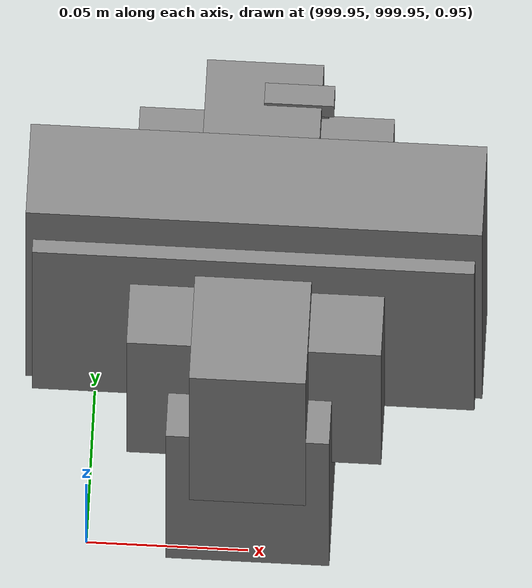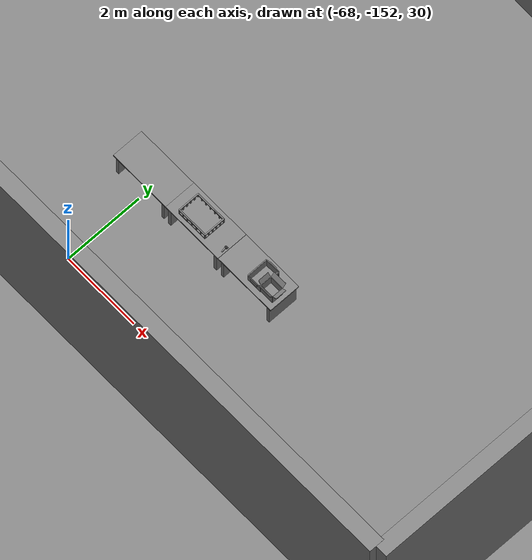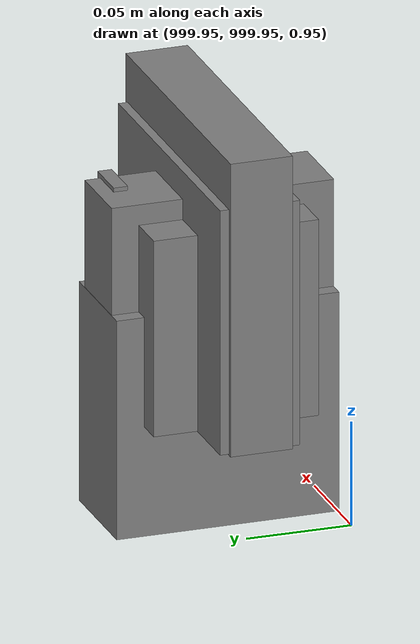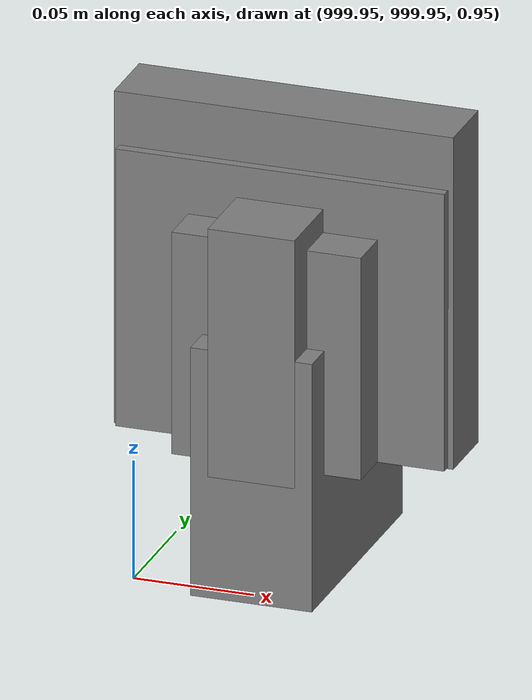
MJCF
<mujoco>
    <option gravity="0.000000000 0.000000000 -9.810000420" timestep="0.0049999999" integrator="implicitfast" density="1.225" viscosity="1.8000001e-05" noslip_iterations="10" iterations="100" sdf_iterations="50">
        <flag multiccd="disable"/>
    </option>
    <size memory="1000M"/>
    <compiler coordinate="local"/>
    <worldbody>
        <light cutoff="30" pos="0 1 1" dir="0 -1 -2"/>
        <light cutoff="30" pos="0 -1 1" dir="0 1 -2"/>
        <body pos="-64.866622925 -149.383972168 30.183746338" euler="89.999984741 89.999946594 0.000000000" name="openloong_gripper_2f85_fix_base_usda_bluebox_01">
            <geom contype="1" conaffinity="1" density="1000" type="box" material="" rgba="0.500000000 0.500000000 0.500000000 1.000000000" solimp="0.899999976 0.949999988 0.001000000" friction="1.000000000 0.005000000 0.000100000" solref="0.020000000 1.000000000" margin="0" condim="3" group="0" pos="0.276580811 0.187225342 0.000068665" quat="0.707106948 0.000077471 0.707106352 0.000077486" size="0.100000001 0.057999998 0.010000000" name="openloong_gripper_2f85_fix_base_usda_geom_E593C021_4487_422D_AB88_4BB18EBDE4C7"/>
            <geom contype="1" conaffinity="1" density="1000" type="box" material="" rgba="0.500000000 0.500000000 0.500000000 1.000000000" solimp="0.899999976 0.949999988 0.001000000" friction="1.000000000 0.005000000 0.000100000" solref="0.020000000 1.000000000" margin="0" condim="3" group="0" pos="0.000000000 0.002883911 0.000000000" quat="0.999999881 0.000000000 0.000000000 0.000000000" size="0.254000008 0.003000000 0.172000006" name="openloong_gripper_2f85_fix_base_usda_geom_A564F9E7_F793_444B_B5EF_9BF3B9DE364E"/>
            <geom contype="1" conaffinity="1" density="1000" type="box" material="" rgba="0.500000000 0.500000000 0.500000000 1.000000000" solimp="0.899999976 0.949999988 0.001000000" friction="1.000000000 0.005000000 0.000100000" solref="0.020000000 1.000000000" margin="0" condim="3" group="0" pos="0.000000000 0.124874115 0.173484802" quat="0.999796331 0.020176515 -0.000000015 0.000000030" size="0.259999990 0.119999997 0.007000000" name="openloong_gripper_2f85_fix_base_usda_geom_63175DD1_5653_40F0_9B69_EAB9C9133BEF"/>
            <geom contype="1" conaffinity="1" density="1000" type="box" material="" rgba="0.500000000 0.500000000 0.500000000 1.000000000" solimp="0.899999976 0.949999988 0.001000000" friction="1.000000000 0.005000000 0.000100000" solref="0.020000000 1.000000000" margin="0" condim="3" group="0" pos="0.000000000 0.124874115 -0.173469543" quat="0.999796331 -0.020176545 -0.000000015 0.000000000" size="0.259999990 0.119999997 0.007000000" name="openloong_gripper_2f85_fix_base_usda_geom_8B90B2E8_8F6A_432C_BA67_37731D47A848"/>
            <geom contype="1" conaffinity="1" density="1000" type="box" material="" rgba="0.500000000 0.500000000 0.500000000 1.000000000" solimp="0.899999976 0.949999988 0.001000000" friction="1.000000000 0.005000000 0.000100000" solref="0.020000000 1.000000000" margin="0" condim="3" group="0" pos="0.000000000 0.214008331 0.188980103" quat="0.999912977 0.013176724 0.000000015 0.000000000" size="0.259999990 0.029999999 0.012500000" name="openloong_gripper_2f85_fix_base_usda_geom_154E0E7F_789F_4A61_9443_5BC446CE3971"/>
            <geom contype="1" conaffinity="1" density="1000" type="box" material="" rgba="0.500000000 0.500000000 0.500000000 1.000000000" solimp="0.899999976 0.949999988 0.001000000" friction="1.000000000 0.005000000 0.000100000" solref="0.020000000 1.000000000" margin="0" condim="3" group="0" pos="-0.258361816 0.125289917 0.001876831" quat="0.702796936 -0.020792112 0.710783124 0.020769298" size="0.189999998 0.119999997 0.009000000" name="openloong_gripper_2f85_fix_base_usda_geom_1561F78F_96AC_4DFB_AEA5_1091818F3A0D"/>
            <geom contype="1" conaffinity="1" density="1000" type="box" material="" rgba="0.500000000 0.500000000 0.500000000 1.000000000" solimp="0.899999976 0.949999988 0.001000000" friction="1.000000000 0.005000000 0.000100000" solref="0.020000000 1.000000000" margin="0" condim="3" group="0" pos="0.000000000 0.214008331 -0.188980103" quat="0.999912977 -0.013176769 0.000000030 0.000000015" size="0.259999990 0.029999999 0.012500000" name="openloong_gripper_2f85_fix_base_usda_geom_9B667740_EC22_404F_A09C_36BA5254D08E"/>
            <geom contype="1" conaffinity="1" density="1000" type="box" material="" rgba="0.500000000 0.500000000 0.500000000 1.000000000" solimp="0.899999976 0.949999988 0.001000000" friction="1.000000000 0.005000000 0.000100000" solref="0.020000000 1.000000000" margin="0" condim="3" group="0" pos="-0.276611328 0.187225342 0.000068665" quat="0.707106650 0.000077441 0.707106709 0.000077456" size="0.100000001 0.057999998 0.010000000" name="openloong_gripper_2f85_fix_base_usda_geom_5B2956D4_AA53_46AF_91FD_A264C32E9D0F"/>
            <geom contype="1" conaffinity="1" density="1000" type="box" material="" rgba="0.500000000 0.500000000 0.500000000 1.000000000" solimp="0.899999976 0.949999988 0.001000000" friction="1.000000000 0.005000000 0.000100000" solref="0.020000000 1.000000000" margin="0" condim="3" group="0" pos="0.258331299 0.125289917 0.001876831" quat="0.702851415 0.018856421 0.710823774 -0.019329369" size="0.189999998 0.119999997 0.009000000" name="openloong_gripper_2f85_fix_base_usda_geom_219B6FDB_1861_4F42_B643_A701F8A0F528"/>
            <freejoint name="openloong_gripper_2f85_fix_base_usda_bluebox_01_joint"/>
            <site size="0.005000000 0.005000000 0.005000000" rgba="0.500000000 0.500000000 0.500000000 1.000000000" pos="0.000000000 0.000000000 0.000000000" quat="0.999961913 0.008726534 0.000000000 0.000000000" group="0" type="sphere" name="openloong_gripper_2f85_fix_base_usda_bluebox_01site"/>
        </body>
        <body pos="-64.496299744 -149.491867065 30.235729218" euler="0.000000000 0.000000000 89.999946594" name="openloong_gripper_2f85_fix_base_usda_cardboardbox_01">
            <geom contype="1" conaffinity="1" density="1000" type="box" material="" rgba="0.500000000 0.500000000 0.500000000 1.000000000" solimp="0.899999976 0.949999988 0.001000000" friction="1.000000000 0.005000000 0.000100000" solref="0.020000000 1.000000000" margin="0" condim="3" group="0" pos="-0.003166199 -0.004086494 0.005052090" quat="1.000000000 0.000000000 0.000000000 0.000000000" size="0.142499998 0.177500010 0.005000000" name="openloong_gripper_2f85_fix_base_usda_geom_82C7718A_D3F6_4868_9BEB_EE790E2773EB"/>
            <geom contype="1" conaffinity="1" density="1000" type="box" material="" rgba="0.500000000 0.500000000 0.500000000 1.000000000" solimp="0.899999976 0.949999988 0.001000000" friction="1.000000000 0.005000000 0.000100000" solref="0.020000000 1.000000000" margin="0" condim="3" group="0" pos="-0.003166199 0.170316696 0.150570869" quat="1.000000000 0.000000000 0.000000000 0.000000000" size="0.142499998 0.005000000 0.149999991" name="openloong_gripper_2f85_fix_base_usda_geom_C6014434_FCB7_473C_AC3D_9E59FC00376B"/>
            <geom contype="1" conaffinity="1" density="1000" type="box" material="" rgba="0.500000000 0.500000000 0.500000000 1.000000000" solimp="0.899999976 0.949999988 0.001000000" friction="1.000000000 0.005000000 0.000100000" solref="0.020000000 1.000000000" margin="0" condim="3" group="0" pos="-0.147399902 -0.005307198 0.150570869" quat="1.000000000 0.000000000 0.000000000 0.000000000" size="0.005000000 0.177500010 0.149999991" name="openloong_gripper_2f85_fix_base_usda_geom_F226DB57_148B_4C74_84F3_69E3F12BA8BE"/>
            <geom contype="1" conaffinity="1" density="1000" type="box" material="" rgba="0.500000000 0.500000000 0.500000000 1.000000000" solimp="0.899999976 0.949999988 0.001000000" friction="1.000000000 0.005000000 0.000100000" solref="0.020000000 1.000000000" margin="0" condim="3" group="0" pos="0.140275955 -0.005307198 0.150570869" quat="1.000000000 0.000000000 0.000000000 0.000000000" size="0.005000000 0.177500010 0.149999991" name="openloong_gripper_2f85_fix_base_usda_geom_8E642C55_24C4_4462_A94B_A499E36B64D8"/>
            <geom contype="1" conaffinity="1" density="1000" type="box" material="" rgba="0.500000000 0.500000000 0.500000000 1.000000000" solimp="0.899999976 0.949999988 0.001000000" friction="1.000000000 0.005000000 0.000100000" solref="0.020000000 1.000000000" margin="0" condim="3" group="0" pos="-0.003166199 -0.181550980 0.150570869" quat="1.000000000 0.000000000 0.000000000 0.000000000" size="0.142499998 0.005000000 0.149999991" name="openloong_gripper_2f85_fix_base_usda_geom_32011C25_841A_4BE1_9F1F_D8EE01C2320D"/>
            <freejoint name="openloong_gripper_2f85_fix_base_usda_cardboardbox_01_joint"/>
            <site size="0.005000000 0.005000000 0.005000000" rgba="0.500000000 0.500000000 0.500000000 1.000000000" pos="0.000000000 0.000000000 0.000000000" quat="0.999961913 0.008726535 0.000000000 0.000000000" group="0" type="sphere" name="openloong_gripper_2f85_fix_base_usda_site_3EA34DFF_C399_4679_93B6_7D4C498A9695"/>
            <body pos="0.139160156 -0.004048347 0.301930904" euler="-179.999954224 49.383502960 179.999954224" name="openloong_gripper_2f85_fix_base_usda_A1_006">
                <geom contype="1" conaffinity="1" density="1000" type="box" material="" rgba="0.500000000 0.500000000 0.500000000 1.000000000" solimp="0.899999976 0.949999988 0.001000000" friction="1.000000000 0.005000000 0.000100000" solref="0.020000000 1.000000000" margin="0" condim="3" group="0" pos="-0.071587563 0.000009537 0.001745224" quat="0.999999881 0.000000000 0.000000000 0.000000000" size="0.071249999 0.179999992 0.002500000" name="openloong_gripper_2f85_fix_base_usda_geom_32EBE0F6_149B_4AE3_9A1A_D74779FF6C1C"/>
                <joint armature="0" stiffness="0.07" damping="0.0099999998" axis="0.000000 1.000000 0.000000" type="hinge" name="openloong_gripper_2f85_fix_base_usda_A1_006"/>
            </body>
            <body pos="-0.145902634 -0.004086494 0.301938057" euler="-180.000000000 -60.000011444 -180.000000000" name="openloong_gripper_2f85_fix_base_usda_A2_006">
                <geom contype="1" conaffinity="1" density="1000" type="box" material="" rgba="0.500000000 0.500000000 0.500000000 1.000000000" solimp="0.899999976 0.949999988 0.001000000" friction="1.000000000 0.005000000 0.000100000" solref="0.020000000 1.000000000" margin="0" condim="3" group="0" pos="0.071268082 0.000009537 0.002717972" quat="0.000002921 0.000000000 -0.000000030 0.999999881" size="0.071249999 0.179999992 0.002500000" name="openloong_gripper_2f85_fix_base_usda_geom_B72A084C_683C_45FA_9239_DFC1F80AB355"/>
                <joint armature="0" stiffness="0.07" damping="0.0099999998" axis="0.000000 1.000000 0.000000" type="hinge" name="openloong_gripper_2f85_fix_base_usda_A2_006"/>
            </body>
            <body pos="-0.003385544 0.175991058 0.301930904" euler="-125.858116150 -0.000004561 0.000002331" name="openloong_gripper_2f85_fix_base_usda_B2_006">
                <geom contype="1" conaffinity="1" density="1000" type="box" material="" rgba="0.500000000 0.500000000 0.500000000 1.000000000" solimp="0.899999976 0.949999988 0.001000000" friction="1.000000000 0.005000000 0.000100000" solref="0.020000000 1.000000000" margin="0" condim="3" group="0" pos="0.000009537 -0.070939064 -0.002470016" quat="0.999614120 0.027776197 -0.000000015 0.000000030" size="0.137500003 0.064999998 0.005000000" name="openloong_gripper_2f85_fix_base_usda_geom_757A9ADA_BC60_44A8_AAED_FFD649812D15"/>
                <joint armature="0" stiffness="0.07" damping="0.0099999998" axis="1.000000 0.000000 0.000000" type="hinge" name="openloong_gripper_2f85_fix_base_usda_B2_006"/>
            </body>
            <body pos="-0.003385544 -0.184140205 0.301938057" euler="147.805557251 0.000000000 0.000000000" name="openloong_gripper_2f85_fix_base_usda_B1_006">
                <geom contype="1" conaffinity="1" density="1000" type="box" material="" rgba="0.500000000 0.500000000 0.500000000 1.000000000" solimp="0.899999976 0.949999988 0.001000000" friction="1.000000000 0.005000000 0.000100000" solref="0.020000000 1.000000000" margin="0" condim="3" group="0" pos="-0.000028610 0.070202351 -0.002703667" quat="0.999614179 -0.027776167 0.000000000 0.000000000" size="0.137500003 0.064999998 0.005000000" name="openloong_gripper_2f85_fix_base_usda_geom_76F7030E_5374_4A7E_B188_417211893E92"/>
                <joint armature="0" stiffness="0.07" damping="0.0099999998" axis="1.000000 0.000000 0.000000" type="hinge" name="openloong_gripper_2f85_fix_base_usda_B1_006"/>
            </body>
        </body>
        <body pos="-65.882858276 -149.481979370 30.229999542" euler="-64.487716675 0.000000000 0.000000000" name="openloong_gripper_2f85_fix_base_usda_Barcode">
            <geom contype="1" conaffinity="1" density="1000" type="box" material="" rgba="0.500000000 0.500000000 0.500000000 1.000000000" solimp="0.899999976 0.949999988 0.001000000" friction="1.000000000 0.005000000 0.000100000" solref="0.020000000 1.000000000" margin="0" condim="3" group="0" pos="0.000000000 0.013038635 0.001419067" quat="0.000000000 0.000000000 0.000000000 1.000000119" size="0.034000002 0.010000000 0.017999999" name="openloong_gripper_2f85_fix_base_usda_geom_6AEA2E15_7453_4BEF_ADD2_59B9F59277B1"/>
            <geom contype="1" conaffinity="1" density="1000" type="box" material="" rgba="0.500000000 0.500000000 0.500000000 1.000000000" solimp="0.899999976 0.949999988 0.001000000" friction="1.000000000 0.005000000 0.000100000" solref="0.020000000 1.000000000" margin="0" condim="3" group="0" pos="0.000000000 -0.035301208 -0.007095337" quat="0.000000000 0.000000000 -0.043619365 0.999048233" size="0.028999999 0.010000000 0.020000000" name="openloong_gripper_2f85_fix_base_usda_geom_F5DD224E_A794_4BD3_8DA6_1EF8E78F867C"/>
            <geom contype="1" conaffinity="1" density="1000" type="box" material="" rgba="0.500000000 0.500000000 0.500000000 1.000000000" solimp="0.899999976 0.949999988 0.001000000" friction="1.000000000 0.005000000 0.000100000" solref="0.020000000 1.000000000" margin="0" condim="3" group="0" pos="0.000000000 -0.043411255 -0.011749268" quat="0.922262907 0.386563420 0.000000000 0.000000000" size="0.026000001 0.010000000 0.020000000" name="openloong_gripper_2f85_fix_base_usda_geom_7430208C_C338_4AAD_B9F2_02663B246963"/>
            <geom contype="1" conaffinity="1" density="1000" type="box" material="" rgba="0.500000000 0.500000000 0.500000000 1.000000000" solimp="0.899999976 0.949999988 0.001000000" friction="1.000000000 0.005000000 0.000100000" solref="0.020000000 1.000000000" margin="0" condim="3" group="0" pos="0.000000000 -0.016967773 -0.031860352" quat="0.000000000 0.000000000 0.000000000 1.000000119" size="0.008000000 0.010000000 0.013000000" name="openloong_gripper_2f85_fix_base_usda_geom_EF426C73_BD58_4E2E_AE83_2FAA7A2E10BD"/>
            <geom contype="1" conaffinity="1" density="1000" type="box" material="" rgba="0.500000000 0.500000000 0.500000000 1.000000000" solimp="0.899999976 0.949999988 0.001000000" friction="1.000000000 0.005000000 0.000100000" solref="0.020000000 1.000000000" margin="0" condim="3" group="0" pos="0.000000000 -0.001869202 0.000312805" quat="0.953716993 0.300705761 0.000000000 0.000000000" size="0.032000002 0.010000000 0.018999999" name="openloong_gripper_2f85_fix_base_usda_geom_DA32A38C_DFD0_4154_9E8C_D1BFD33FD280"/>
            <geom contype="1" conaffinity="1" density="1000" type="box" material="" rgba="0.500000000 0.500000000 0.500000000 1.000000000" solimp="0.899999976 0.949999988 0.001000000" friction="1.000000000 0.005000000 0.000100000" solref="0.020000000 1.000000000" margin="0" condim="3" group="0" pos="0.000000000 -0.019531250 -0.003173828" quat="0.953716993 0.300705761 0.000000000 0.000000000" size="0.030999999 0.010000000 0.020000000" name="openloong_gripper_2f85_fix_base_usda_geom_BBCEBAB9_0665_4A84_928C_DD79602C1902"/>
            <geom contype="1" conaffinity="1" density="1000" type="box" material="" rgba="0.500000000 0.500000000 0.500000000 1.000000000" solimp="0.899999976 0.949999988 0.001000000" friction="1.000000000 0.005000000 0.000100000" solref="0.020000000 1.000000000" margin="0" condim="3" group="0" pos="0.000000000 -0.035301208 -0.007095337" quat="0.953716993 0.300705761 0.000000000 0.000000000" size="0.028999999 0.010000000 0.020000000" name="openloong_gripper_2f85_fix_base_usda_geom_1068D5C1_28E0_40F4_BED7_0D9853450BA9"/>
            <geom contype="1" conaffinity="1" density="1000" type="box" material="" rgba="0.500000000 0.500000000 0.500000000 1.000000000" solimp="0.899999976 0.949999988 0.001000000" friction="1.000000000 0.005000000 0.000100000" solref="0.020000000 1.000000000" margin="0" condim="3" group="0" pos="0.000000000 -0.042617798 -0.071121216" quat="0.000000000 0.000000000 0.000000000 1.000000119" size="0.013000000 0.021000000 0.059999999" name="openloong_gripper_2f85_fix_base_usda_geom_95ADFC5B_1F41_4E90_870B_C77A3058AF3F"/>
            <freejoint name="openloong_gripper_2f85_fix_base_usda_Barcode_joint"/>
            <site size="0.005000000 0.005000000 0.005000000" rgba="0.500000000 0.500000000 0.500000000 1.000000000" pos="0.000000000 0.000000000 0.000000000" quat="1.000000000 0.000000000 0.000000000 0.000000000" group="0" type="sphere" name="openloong_gripper_2f85_fix_base_usda_Barcode_site"/>
        </body>
        <body pos="-66.745018005 -149.392349243 30.184000015" euler="0.000000000 0.000000000 89.999946594" name="[22331179204927]_Basket_01">
            <geom contype="1" conaffinity="1" density="1000" type="box" material="" rgba="0.500000000 0.500000000 0.500000000 1.000000000" solimp="0.899999976 0.949999988 0.001000000" friction="1.000000000 0.005000000 0.000100000" solref="0.020000000 1.000000000" margin="0" condim="3" group="0" pos="-0.052425385 0.389207840 0.089787483" quat="0.707107008 0.000000000 0.000000000 0.707106411" size="0.014249999 0.014249999 0.059999999" name="[22331179204927]_geom_E3935FAE_3ED7_4250_A67B_0404BBD03EF6"/>
            <geom contype="1" conaffinity="1" density="1000" type="box" material="" rgba="0.500000000 0.500000000 0.500000000 1.000000000" solimp="0.899999976 0.949999988 0.001000000" friction="1.000000000 0.005000000 0.000100000" solref="0.020000000 1.000000000" margin="0" condim="3" group="0" pos="0.264015198 -0.133043289 0.089787483" quat="0.707107008 0.000000000 0.000000000 0.707106411" size="0.014249999 0.014249999 0.059999999" name="[22331179204927]_geom_219FE3B4_99EF_4024_A45D_BC421C52DE7C"/>
            <geom contype="1" conaffinity="1" density="1000" type="box" material="" rgba="0.500000000 0.500000000 0.500000000 1.000000000" solimp="0.899999976 0.949999988 0.001000000" friction="1.000000000 0.005000000 0.000100000" solref="0.020000000 1.000000000" margin="0" condim="3" group="0" pos="-0.264015198 -0.265548706 0.089793205" quat="0.707107008 0.000000000 0.000000000 0.707106411" size="0.014249999 0.014249999 0.059999999" name="[22331179204927]_geom_FC608B3E_9D2B_4AF6_A142_F8B63707EE39"/>
            <geom contype="1" conaffinity="1" density="1000" type="box" material="" rgba="0.500000000 0.500000000 0.500000000 1.000000000" solimp="0.899999976 0.949999988 0.001000000" friction="1.000000000 0.005000000 0.000100000" solref="0.020000000 1.000000000" margin="0" condim="3" group="0" pos="-0.160263062 -0.389322281 0.089793205" quat="0.707107008 0.000000000 0.000000000 0.707106411" size="0.014249999 0.014249999 0.059999999" name="[22331179204927]_geom_CA7E623C_B4AE_4B91_AF35_EB37E8F38363"/>
            <geom contype="1" conaffinity="1" density="1000" type="box" material="" rgba="0.500000000 0.500000000 0.500000000 1.000000000" solimp="0.899999976 0.949999988 0.001000000" friction="1.000000000 0.005000000 0.000100000" solref="0.020000000 1.000000000" margin="0" condim="3" group="0" pos="0.162265778 -0.389322281 0.089787483" quat="0.707107008 0.000000000 0.000000000 0.707106411" size="0.014249999 0.014249999 0.059999999" name="[22331179204927]_geom_770FCC1A_6E7D_48B1_8579_E1FAA36AE8E6"/>
            <geom contype="1" conaffinity="1" density="1000" type="box" material="" rgba="0.500000000 0.500000000 0.500000000 1.000000000" solimp="0.899999976 0.949999988 0.001000000" friction="1.000000000 0.005000000 0.000100000" solref="0.020000000 1.000000000" margin="0" condim="3" group="0" pos="0.264015198 0.389207840 0.089787483" quat="0.707107008 0.000000000 0.000000000 0.707106411" size="0.014249999 0.014249999 0.059999999" name="[22331179204927]_geom_35532191_3D99_4A36_A3E4_CD071E231B45"/>
            <geom contype="1" conaffinity="1" density="1000" type="box" material="" rgba="0.500000000 0.500000000 0.500000000 1.000000000" solimp="0.899999976 0.949999988 0.001000000" friction="1.000000000 0.005000000 0.000100000" solref="0.020000000 1.000000000" margin="0" condim="3" group="0" pos="-0.264015198 -0.133043289 0.089793205" quat="0.707107008 0.000000000 0.000000000 0.707106411" size="0.014249999 0.014249999 0.059999999" name="[22331179204927]_geom_F4429220_76BF_45C1_B041_E49ABC51639D"/>
            <geom contype="1" conaffinity="1" density="1000" type="box" material="" rgba="0.500000000 0.500000000 0.500000000 1.000000000" solimp="0.899999976 0.949999988 0.001000000" friction="1.000000000 0.005000000 0.000100000" solref="0.020000000 1.000000000" margin="0" condim="3" group="0" pos="-0.264026642 0.269256592 0.089793205" quat="0.707107008 0.000000000 0.000000000 0.707106411" size="0.014249999 0.014249999 0.059999999" name="[22331179204927]_geom_90796580_2532_4978_B726_A37FB98E6A86"/>
            <geom contype="1" conaffinity="1" density="1000" type="box" material="" rgba="0.500000000 0.500000000 0.500000000 1.000000000" solimp="0.899999976 0.949999988 0.001000000" friction="1.000000000 0.005000000 0.000100000" solref="0.020000000 1.000000000" margin="0" condim="3" group="0" pos="0.054462433 0.389207840 0.089787483" quat="0.707107008 0.000000000 0.000000000 0.707106411" size="0.014249999 0.014249999 0.059999999" name="[22331179204927]_geom_B9DD9501_8E46_4CF3_9144_C94BDCAE8E3D"/>
            <geom contype="1" conaffinity="1" density="1000" type="box" material="" rgba="0.500000000 0.500000000 0.500000000 1.000000000" solimp="0.899999976 0.949999988 0.001000000" friction="1.000000000 0.005000000 0.000100000" solref="0.020000000 1.000000000" margin="0" condim="3" group="0" pos="0.054462433 -0.389322281 0.089787483" quat="0.707107008 0.000000000 0.000000000 0.707106411" size="0.014249999 0.014249999 0.059999999" name="[22331179204927]_geom_2FB13FB0_C506_419C_9FD8_675E35D20ACD"/>
            <geom contype="1" conaffinity="1" density="1000" type="box" material="" rgba="0.500000000 0.500000000 0.500000000 1.000000000" solimp="0.899999976 0.949999988 0.001000000" friction="1.000000000 0.005000000 0.000100000" solref="0.020000000 1.000000000" margin="0" condim="3" group="0" pos="0.264015198 0.269256592 0.089793205" quat="0.707107008 0.000000000 0.000000000 0.707106411" size="0.014249999 0.014249999 0.059999999" name="[22331179204927]_geom_954970E2_E7EF_4321_A010_D14A9039A145"/>
            <geom contype="1" conaffinity="1" density="1000" type="box" material="" rgba="0.500000000 0.500000000 0.500000000 1.000000000" solimp="0.899999976 0.949999988 0.001000000" friction="1.000000000 0.005000000 0.000100000" solref="0.020000000 1.000000000" margin="0" condim="3" group="0" pos="0.264015198 -0.389322281 0.089787483" quat="0.707107008 0.000000000 0.000000000 0.707106411" size="0.014249999 0.014249999 0.059999999" name="[22331179204927]_geom_C82E6183_250E_4153_AB6E_46C6B3BD278C"/>
            <geom contype="1" conaffinity="1" density="1000" type="box" material="" rgba="0.500000000 0.500000000 0.500000000 1.000000000" solimp="0.899999976 0.949999988 0.001000000" friction="1.000000000 0.005000000 0.000100000" solref="0.020000000 1.000000000" margin="0" condim="3" group="0" pos="0.000000000 0.000000000 0.015998840" quat="0.707107008 0.000000000 0.000000000 0.707106411" size="0.403499991 0.279000014 0.015750000" name="[22331179204927]_geom_5F9AA5E3_3393_47BD_A120_F0E9236886BB"/>
            <geom contype="1" conaffinity="1" density="1000" type="box" material="" rgba="0.500000000 0.500000000 0.500000000 1.000000000" solimp="0.899999976 0.949999988 0.001000000" friction="1.000000000 0.005000000 0.000100000" solref="0.020000000 1.000000000" margin="0" condim="3" group="0" pos="0.000000000 -0.389476776 0.163619041" quat="0.707107008 0.000000000 0.000000000 0.707106411" size="0.015000000 0.277500004 0.015750000" name="[22331179204927]_geom_5E02A837_DC82_4EEA_A371_D7975E2D66CD"/>
            <geom contype="1" conaffinity="1" density="1000" type="box" material="" rgba="0.500000000 0.500000000 0.500000000 1.000000000" solimp="0.899999976 0.949999988 0.001000000" friction="1.000000000 0.005000000 0.000100000" solref="0.020000000 1.000000000" margin="0" condim="3" group="0" pos="0.162265778 0.389207840 0.089787483" quat="0.707107008 0.000000000 0.000000000 0.707106411" size="0.014249999 0.014249999 0.059999999" name="[22331179204927]_geom_F61E8850_16B4_46EA_8EAA_EAF6A9C34A9B"/>
            <geom contype="1" conaffinity="1" density="1000" type="box" material="" rgba="0.500000000 0.500000000 0.500000000 1.000000000" solimp="0.899999976 0.949999988 0.001000000" friction="1.000000000 0.005000000 0.000100000" solref="0.020000000 1.000000000" margin="0" condim="3" group="0" pos="0.000000000 0.389471054 0.163619041" quat="0.707107008 0.000000000 0.000000000 0.707106411" size="0.015000000 0.277500004 0.015750000" name="[22331179204927]_geom_E8B029FE_5E44_4D9E_AB9E_0F6972247E8F"/>
            <geom contype="1" conaffinity="1" density="1000" type="box" material="" rgba="0.500000000 0.500000000 0.500000000 1.000000000" solimp="0.899999976 0.949999988 0.001000000" friction="1.000000000 0.005000000 0.000100000" solref="0.020000000 1.000000000" margin="0" condim="3" group="0" pos="-0.263511658 0.000000000 0.163619041" quat="0.707107008 0.000000000 0.000000000 0.707106411" size="0.403499991 0.015000000 0.015750000" name="[22331179204927]_geom_8A7E1BFD_9D2B_44CE_9DF0_508837496023"/>
            <geom contype="1" conaffinity="1" density="1000" type="box" material="" rgba="0.500000000 0.500000000 0.500000000 1.000000000" solimp="0.899999976 0.949999988 0.001000000" friction="1.000000000 0.005000000 0.000100000" solref="0.020000000 1.000000000" margin="0" condim="3" group="0" pos="-0.264015198 0.141334534 0.089793205" quat="0.707107008 0.000000000 0.000000000 0.707106411" size="0.014249999 0.014249999 0.059999999" name="[22331179204927]_geom_E29AD34C_9253_4134_9DCF_825BF9C642C5"/>
            <geom contype="1" conaffinity="1" density="1000" type="box" material="" rgba="0.500000000 0.500000000 0.500000000 1.000000000" solimp="0.899999976 0.949999988 0.001000000" friction="1.000000000 0.005000000 0.000100000" solref="0.020000000 1.000000000" margin="0" condim="3" group="0" pos="0.264015198 -0.265548706 0.089787483" quat="0.707107008 0.000000000 0.000000000 0.707106411" size="0.014249999 0.014249999 0.059999999" name="[22331179204927]_geom_267ED394_D1B1_4E11_A09F_F694BC366FA7"/>
            <geom contype="1" conaffinity="1" density="1000" type="box" material="" rgba="0.500000000 0.500000000 0.500000000 1.000000000" solimp="0.899999976 0.949999988 0.001000000" friction="1.000000000 0.005000000 0.000100000" solref="0.020000000 1.000000000" margin="0" condim="3" group="0" pos="-0.160263062 0.389207840 0.089787483" quat="0.707107008 0.000000000 0.000000000 0.707106411" size="0.014249999 0.014249999 0.059999999" name="[22331179204927]_geom_9B4A3479_7096_4D3F_9D1D_E776BD24ED0D"/>
            <geom contype="1" conaffinity="1" density="1000" type="box" material="" rgba="0.500000000 0.500000000 0.500000000 1.000000000" solimp="0.899999976 0.949999988 0.001000000" friction="1.000000000 0.005000000 0.000100000" solref="0.020000000 1.000000000" margin="0" condim="3" group="0" pos="-0.052425385 -0.389322281 0.089787483" quat="0.707107008 0.000000000 0.000000000 0.707106411" size="0.014249999 0.014249999 0.059999999" name="[22331179204927]_geom_C377C1E9_9EE5_4023_A45F_DE358561329C"/>
            <geom contype="1" conaffinity="1" density="1000" type="box" material="" rgba="0.500000000 0.500000000 0.500000000 1.000000000" solimp="0.899999976 0.949999988 0.001000000" friction="1.000000000 0.005000000 0.000100000" solref="0.020000000 1.000000000" margin="0" condim="3" group="0" pos="-0.264026642 -0.389322281 0.089793205" quat="0.707107008 0.000000000 0.000000000 0.707106411" size="0.014249999 0.014249999 0.059999999" name="[22331179204927]_geom_F3C9C997_1A8D_476B_976A_47BC944A081B"/>
            <geom contype="1" conaffinity="1" density="1000" type="box" material="" rgba="0.500000000 0.500000000 0.500000000 1.000000000" solimp="0.899999976 0.949999988 0.001000000" friction="1.000000000 0.005000000 0.000100000" solref="0.020000000 1.000000000" margin="0" condim="3" group="0" pos="0.264015198 0.141334534 0.089787483" quat="0.707107008 0.000000000 0.000000000 0.707106411" size="0.014249999 0.014249999 0.059999999" name="[22331179204927]_geom_EEB13D00_8E52_4DBC_945C_6829CD969C0F"/>
            <geom contype="1" conaffinity="1" density="1000" type="box" material="" rgba="0.500000000 0.500000000 0.500000000 1.000000000" solimp="0.899999976 0.949999988 0.001000000" friction="1.000000000 0.005000000 0.000100000" solref="0.020000000 1.000000000" margin="0" condim="3" group="0" pos="-0.264015198 0.389207840 0.089793205" quat="0.707107008 0.000000000 0.000000000 0.707106411" size="0.014249999 0.014249999 0.059999999" name="[22331179204927]_geom_F0FBD96C_0312_417B_9B82_111B5299B342"/>
            <geom contype="1" conaffinity="1" density="1000" type="box" material="" rgba="0.500000000 0.500000000 0.500000000 1.000000000" solimp="0.899999976 0.949999988 0.001000000" friction="1.000000000 0.005000000 0.000100000" solref="0.020000000 1.000000000" margin="0" condim="3" group="0" pos="0.264015198 0.004480362 0.089787483" quat="0.707107008 0.000000000 0.000000000 0.707106411" size="0.014249999 0.014249999 0.059999999" name="[22331179204927]_geom_90F10519_BA57_4331_941C_534235B20D41"/>
            <geom contype="1" conaffinity="1" density="1000" type="box" material="" rgba="0.500000000 0.500000000 0.500000000 1.000000000" solimp="0.899999976 0.949999988 0.001000000" friction="1.000000000 0.005000000 0.000100000" solref="0.020000000 1.000000000" margin="0" condim="3" group="0" pos="0.263694763 -0.000011444 0.163619041" quat="0.707107008 0.000000000 0.000000000 0.707106411" size="0.403499991 0.015000000 0.015750000" name="[22331179204927]_geom_B70AD765_2B45_49C8_895E_4D15DCEA91DE"/>
            <geom contype="1" conaffinity="1" density="1000" type="box" material="" rgba="0.500000000 0.500000000 0.500000000 1.000000000" solimp="0.899999976 0.949999988 0.001000000" friction="1.000000000 0.005000000 0.000100000" solref="0.020000000 1.000000000" margin="0" condim="3" group="0" pos="-0.264015198 0.004480362 0.089793205" quat="0.707107008 0.000000000 0.000000000 0.707106411" size="0.014249999 0.014249999 0.059999999" name="[22331179204927]_geom_F26587BA_C6CB_43B9_9BF0_113FDCCEB22D"/>
            <freejoint name="[22331179204927]_joint_1F95525E_3B93_45DC_BE9C_E1B5A8C78DCB"/>
        </body>
        <body pos="0.000000000 0.000000000 0.000000000" euler="0.000000000 0.000000000 0.000000000" name="Static Objects_Static Objects">
            <geom contype="1" conaffinity="1" density="1000" type="box" material="" rgba="0.500000000 0.500000000 0.500000000 1.000000000" solimp="0.899999976 0.949999988 0.001000000" friction="1.000000000 0.005000000 0.000100000" solref="0.020000000 1.000000000" margin="0" condim="3" group="0" pos="-67.544113159 -149.365814209 29.727830887" quat="0.500000417 0.499999970 0.499999553 0.499999970" size="0.381000012 0.319999993 0.041000001" name="Static Objects_geom_FA10B1EE_0FEC_4243_9394_BD08502A438A"/>
            <geom contype="1" conaffinity="1" density="1000" type="box" material="" rgba="0.500000000 0.500000000 0.500000000 1.000000000" solimp="0.899999976 0.949999988 0.001000000" friction="1.000000000 0.005000000 0.000100000" solref="0.020000000 1.000000000" margin="0" condim="3" group="0" pos="-68.239501953 -149.365814209 30.086868286" quat="0.500000417 0.499999970 0.499999553 0.499999970" size="0.370999992 0.039500002 0.745000005" name="Static Objects_geom_61ABF2FF_8D3F_4E25_8E95_CF865C0263FA"/>
            <geom contype="1" conaffinity="1" density="1000" type="box" material="" rgba="0.500000000 0.500000000 0.500000000 1.000000000" solimp="0.899999976 0.949999988 0.001000000" friction="1.000000000 0.005000000 0.000100000" solref="0.020000000 1.000000000" margin="0" condim="3" group="0" pos="-68.239501953 -149.365814209 30.147235870" quat="0.500000417 0.499999970 0.499999553 0.499999970" size="0.400000006 0.022000000 0.800000012" name="Static Objects_geom_559457D1_C413_441A_BCC0_50F294E1B616"/>
            <geom contype="1" conaffinity="1" density="1000" type="box" material="" rgba="0.500000000 0.500000000 0.500000000 1.000000000" solimp="0.899999976 0.949999988 0.001000000" friction="1.000000000 0.005000000 0.000100000" solref="0.020000000 1.000000000" margin="0" condim="3" group="0" pos="-68.934890747 -149.365814209 29.727830887" quat="0.500000417 0.499999970 0.499999553 0.499999970" size="0.381000012 0.319999993 0.041000001" name="Static Objects_geom_24F7F262_70E1_4C2A_8EC9_F4116AD232F9"/>
            <geom contype="1" conaffinity="1" density="1000" type="box" material="" rgba="0.500000000 0.500000000 0.500000000 1.000000000" solimp="0.899999976 0.949999988 0.001000000" friction="1.000000000 0.005000000 0.000100000" solref="0.020000000 1.000000000" margin="0" condim="3" group="0" pos="-68.239501953 -149.365814209 29.561563492" quat="0.500000417 0.499999970 0.499999553 0.499999970" size="0.020000000 0.022000000 0.660000026" name="Static Objects_geom_3B6D2762_B786_41E1_8DCC_7AE76E50EB6E"/>
            <geom contype="1" conaffinity="1" density="1000" type="box" material="" rgba="0.500000000 0.500000000 0.500000000 1.000000000" solimp="0.899999976 0.949999988 0.001000000" friction="1.000000000 0.005000000 0.000100000" solref="0.020000000 1.000000000" margin="0" condim="3" group="0" pos="-65.945671082 -149.365814209 29.727830887" quat="0.500000417 0.499999970 0.499999553 0.499999970" size="0.381000012 0.319999993 0.041000001" name="Static Objects_geom_3A86876C_E38D_497F_B44C_1F1A0E8B67B5"/>
            <geom contype="1" conaffinity="1" density="1000" type="box" material="" rgba="0.500000000 0.500000000 0.500000000 1.000000000" solimp="0.899999976 0.949999988 0.001000000" friction="1.000000000 0.005000000 0.000100000" solref="0.020000000 1.000000000" margin="0" condim="3" group="0" pos="-66.641059875 -149.365814209 30.086868286" quat="0.500000417 0.499999970 0.499999553 0.499999970" size="0.370999992 0.039500002 0.745000005" name="Static Objects_geom_60FF1316_6C5F_47C0_A55D_F823F3788EF4"/>
            <geom contype="1" conaffinity="1" density="1000" type="box" material="" rgba="0.500000000 0.500000000 0.500000000 1.000000000" solimp="0.899999976 0.949999988 0.001000000" friction="1.000000000 0.005000000 0.000100000" solref="0.020000000 1.000000000" margin="0" condim="3" group="0" pos="-66.641059875 -149.365814209 30.147235870" quat="0.500000417 0.499999970 0.499999553 0.499999970" size="0.400000006 0.022000000 0.800000012" name="Static Objects_geom_541CCE68_781D_42E6_96C8_62B8CCB4E167"/>
            <geom contype="1" conaffinity="1" density="1000" type="box" material="" rgba="0.500000000 0.500000000 0.500000000 1.000000000" solimp="0.899999976 0.949999988 0.001000000" friction="1.000000000 0.005000000 0.000100000" solref="0.020000000 1.000000000" margin="0" condim="3" group="0" pos="-67.336448669 -149.365814209 29.727830887" quat="0.500000417 0.499999970 0.499999553 0.499999970" size="0.381000012 0.319999993 0.041000001" name="Static Objects_geom_2DBFFA53_59EF_4892_A55E_FCC32DA46E12"/>
            <geom contype="1" conaffinity="1" density="1000" type="box" material="" rgba="0.500000000 0.500000000 0.500000000 1.000000000" solimp="0.899999976 0.949999988 0.001000000" friction="1.000000000 0.005000000 0.000100000" solref="0.020000000 1.000000000" margin="0" condim="3" group="0" pos="-66.641059875 -149.365814209 29.561563492" quat="0.500000417 0.499999970 0.499999553 0.499999970" size="0.020000000 0.022000000 0.660000026" name="Static Objects_geom_92C8777B_9AFB_41F4_B747_FB99CF7E9962"/>
            <geom contype="1" conaffinity="1" density="1000" type="box" material="" rgba="0.500000000 0.500000000 0.500000000 1.000000000" solimp="0.899999976 0.949999988 0.001000000" friction="1.000000000 0.005000000 0.000100000" solref="0.020000000 1.000000000" margin="0" condim="3" group="0" pos="-64.338577271 -149.365814209 29.727830887" quat="0.500000417 0.499999970 0.499999553 0.499999970" size="0.381000012 0.319999993 0.041000001" name="Static Objects_geom_52EB57A9_9725_44EF_821C_FE60C0DF9100"/>
            <geom contype="1" conaffinity="1" density="1000" type="box" material="" rgba="0.500000000 0.500000000 0.500000000 1.000000000" solimp="0.899999976 0.949999988 0.001000000" friction="1.000000000 0.005000000 0.000100000" solref="0.020000000 1.000000000" margin="0" condim="3" group="0" pos="-65.033966064 -149.365814209 30.086868286" quat="0.500000417 0.499999970 0.499999553 0.499999970" size="0.370999992 0.039500002 0.745000005" name="Static Objects_geom_DF7D018A_51B6_447E_B4FB_665016326D39"/>
            <geom contype="1" conaffinity="1" density="1000" type="box" material="" rgba="0.500000000 0.500000000 0.500000000 1.000000000" solimp="0.899999976 0.949999988 0.001000000" friction="1.000000000 0.005000000 0.000100000" solref="0.020000000 1.000000000" margin="0" condim="3" group="0" pos="-65.033966064 -149.365814209 30.147235870" quat="0.500000417 0.499999970 0.499999553 0.499999970" size="0.400000006 0.022000000 0.800000012" name="Static Objects_geom_A174A03C_E5A0_4539_9FFE_96FCDFA8A6B9"/>
            <geom contype="1" conaffinity="1" density="1000" type="box" material="" rgba="0.500000000 0.500000000 0.500000000 1.000000000" solimp="0.899999976 0.949999988 0.001000000" friction="1.000000000 0.005000000 0.000100000" solref="0.020000000 1.000000000" margin="0" condim="3" group="0" pos="-65.729354858 -149.365814209 29.727830887" quat="0.500000417 0.499999970 0.499999553 0.499999970" size="0.381000012 0.319999993 0.041000001" name="Static Objects_geom_5AE46F53_4C81_40EC_B63C_344C7A3F69C9"/>
            <geom contype="1" conaffinity="1" density="1000" type="box" material="" rgba="0.500000000 0.500000000 0.500000000 1.000000000" solimp="0.899999976 0.949999988 0.001000000" friction="1.000000000 0.005000000 0.000100000" solref="0.020000000 1.000000000" margin="0" condim="3" group="0" pos="-65.033966064 -149.365814209 29.561563492" quat="0.500000417 0.499999970 0.499999553 0.499999970" size="0.020000000 0.022000000 0.660000026" name="Static Objects_geom_9855A948_EAF5_4A71_BE07_5354FCE3766E"/>
            <geom contype="1" conaffinity="1" density="1000" type="box" material="" rgba="0.500000000 0.500000000 0.500000000 1.000000000" solimp="0.899999976 0.949999988 0.001000000" friction="1.000000000 0.005000000 0.000100000" solref="0.020000000 1.000000000" margin="0" condim="3" group="0" pos="-61.754566193 -137.853729248 33.906845093" quat="0.707107067 0.000000000 0.000000000 0.707106471" size="0.759999990 0.759999990 4.500000000" name="Static Objects_geom_659DCA45_A39A_418C_82E3_6898BD3C21B6"/>
            <geom contype="1" conaffinity="1" density="1000" type="box" material="" rgba="0.500000000 0.500000000 0.500000000 1.000000000" solimp="0.899999976 0.949999988 0.001000000" friction="1.000000000 0.005000000 0.000100000" solref="0.020000000 1.000000000" margin="0" condim="3" group="0" pos="-57.511135101 -144.927108765 31.707921982" quat="1.000000000 0.000000000 0.000000000 0.000000000" size="0.200000003 8.000000000 2.299999952" name="Static Objects_geom_1F6DBBB4_72C8_4A79_80A7_37E1293F4086"/>
            <geom contype="1" conaffinity="1" density="1000" type="box" material="" rgba="0.500000000 0.500000000 0.500000000 1.000000000" solimp="0.899999976 0.949999988 0.001000000" friction="1.000000000 0.005000000 0.000100000" solref="0.020000000 1.000000000" margin="0" condim="3" group="0" pos="-80.517646790 -157.574050903 31.688196182" quat="0.707107067 0.000000000 0.000000000 0.707106471" size="0.600000024 0.600000024 2.299999952" name="Static Objects_geom_23C1594D_62BB_4325_843C_30D13751F1F7"/>
            <geom contype="1" conaffinity="1" density="1000" type="box" material="" rgba="0.500000000 0.500000000 0.500000000 1.000000000" solimp="0.899999976 0.949999988 0.001000000" friction="1.000000000 0.005000000 0.000100000" solref="0.020000000 1.000000000" margin="0" condim="3" group="0" pos="-80.711044312 -147.414932251 31.666158676" quat="1.000000000 0.000000000 0.000000000 0.000000000" size="0.200000003 10.000000000 2.299999952" name="Static Objects_geom_C6D190A3_F1DB_48F0_8578_6FC96CF9539A"/>
            <geom contype="1" conaffinity="1" density="1000" type="box" material="" rgba="0.500000000 0.500000000 0.500000000 1.000000000" solimp="0.899999976 0.949999988 0.001000000" friction="1.000000000 0.005000000 0.000100000" solref="0.020000000 1.000000000" margin="0" condim="3" group="0" pos="-57.687217712 -137.434692383 31.688196182" quat="0.707107067 0.000000000 0.000000000 0.707106471" size="0.600000024 0.600000024 2.299999952" name="Static Objects_geom_F11567E7_A436_4817_BB1F_58D1A49263E3"/>
            <geom contype="1" conaffinity="1" density="1000" type="box" material="" rgba="0.500000000 0.500000000 0.500000000 1.000000000" solimp="0.899999976 0.949999988 0.001000000" friction="1.000000000 0.005000000 0.000100000" solref="0.020000000 1.000000000" margin="0" condim="3" group="0" pos="-69.537033081 -140.263229370 31.714921951" quat="0.707107067 0.000000000 0.000000000 0.707106471" size="0.759999990 4.500000000 2.299999952" name="Static Objects_geom_31305A20_E96C_406F_AEB2_FB3F75D82728"/>
            <geom contype="1" conaffinity="1" density="1000" type="box" material="" rgba="0.500000000 0.500000000 0.500000000 1.000000000" solimp="0.899999976 0.949999988 0.001000000" friction="1.000000000 0.005000000 0.000100000" solref="0.020000000 1.000000000" margin="0" condim="3" group="0" pos="-80.073638916 -137.853713989 33.906845093" quat="0.707107067 0.000000000 0.000000000 0.707106471" size="0.759999990 0.759999990 4.500000000" name="Static Objects_geom_B1531B2A_7992_4408_948B_C804D81C3DA3"/>
            <geom contype="1" conaffinity="1" density="1000" type="box" material="" rgba="0.500000000 0.500000000 0.500000000 1.000000000" solimp="0.899999976 0.949999988 0.001000000" friction="1.000000000 0.005000000 0.000100000" solref="0.020000000 1.000000000" margin="0" condim="3" group="0" pos="-73.406707764 -155.734664917 31.707921982" quat="1.000000000 0.000000000 0.000000000 0.000000000" size="0.200000003 3.000000000 2.299999952" name="Static Objects_geom_4F694D4E_CEE3_4298_B4EE_13DC61284F38"/>
            <geom contype="1" conaffinity="1" density="1000" type="box" material="" rgba="0.500000000 0.500000000 0.500000000 1.000000000" solimp="0.899999976 0.949999988 0.001000000" friction="1.000000000 0.005000000 0.000100000" solref="0.020000000 1.000000000" margin="0" condim="3" group="0" pos="-68.497543335 -137.448257446 31.707921982" quat="0.707107067 0.000000000 0.000000000 0.707106471" size="0.200000003 14.000000000 2.299999952" name="Static Objects_geom_BC01B3B4_DFF9_488C_BA35_4E865C01A36C"/>
            <geom contype="1" conaffinity="1" density="1000" type="cylinder" material="" rgba="0.500000000 0.500000000 0.500000000 1.000000000" solimp="0.899999976 0.949999988 0.001000000" friction="1.000000000 0.005000000 0.000100000" solref="0.020000000 1.000000000" margin="0" condim="3" group="0" pos="-68.868522644 -142.134506226 31.711090088" quat="0.707107067 0.000000000 0.000000000 0.707106471" size="0.509999990 2.299999952 1.000000000" name="Static Objects_geom_4E71D1E3_F53E_45D4_B1C2_9C414E429366"/>
            <geom contype="1" conaffinity="1" density="1000" type="plane" material="" rgba="0.500000000 0.500000000 0.500000000 1.000000000" solimp="0.899999976 0.949999988 0.001000000" friction="1.000000000 0.005000000 0.000100000" solref="0.020000000 1.000000000" margin="0" condim="3" group="0" pos="-72.873703003 -147.131927490 29.409669876" quat="1.000000000 0.000000000 0.000000000 0.000000000" size="18.000000000 14.000000000 1.000000000" name="Static Objects_geom_FA6726EA_9AE7_4252_89A7_7AE8DEE99F02"/>
            <geom contype="1" conaffinity="1" density="1000" type="box" material="" rgba="0.500000000 0.500000000 0.500000000 1.000000000" solimp="0.899999976 0.949999988 0.001000000" friction="1.000000000 0.005000000 0.000100000" solref="0.020000000 1.000000000" margin="0" condim="3" group="0" pos="-79.943580627 -157.782272339 31.707921982" quat="0.707107067 0.000000000 0.000000000 0.707106471" size="0.200000003 7.000000000 2.299999952" name="Static Objects_geom_063B07A0_8032_4DFE_8FD1_342484A0D2CA"/>
            <geom contype="1" conaffinity="1" density="1000" type="box" material="" rgba="0.500000000 0.500000000 0.500000000 1.000000000" solimp="0.899999976 0.949999988 0.001000000" friction="1.000000000 0.005000000 0.000100000" solref="0.020000000 1.000000000" margin="0" condim="3" group="0" pos="-65.421028137 -152.903442383 31.707921982" quat="0.707107067 0.000000000 0.000000000 0.707106471" size="0.200000003 7.800000191 2.299999952" name="Static Objects_geom_66DB0194_F191_4B79_B6AE_E02C93DFEF0B"/>
            <geom contype="1" conaffinity="1" density="1000" type="box" material="" rgba="0.500000000 0.500000000 0.500000000 1.000000000" solimp="0.899999976 0.949999988 0.001000000" friction="1.000000000 0.005000000 0.000100000" solref="0.020000000 1.000000000" margin="0" condim="3" group="0" pos="-74.776908875 -149.964416504 31.688196182" quat="1.000000000 0.000000000 0.000000000 0.000000000" size="0.600000024 0.409999996 2.299999952" name="Static Objects_geom_F6AD2B42_D976_441C_B27F_5D6D321FA758"/>
            <geom contype="1" conaffinity="1" density="1000" type="cylinder" material="" rgba="0.500000000 0.500000000 0.500000000 1.000000000" solimp="0.899999976 0.949999988 0.001000000" friction="1.000000000 0.005000000 0.000100000" solref="0.020000000 1.000000000" margin="0" condim="3" group="0" pos="-60.161884308 -142.134506226 31.711090088" quat="0.707107067 0.000000000 0.000000000 0.707106471" size="0.509999990 2.299999952 1.000000000" name="Static Objects_geom_94EFA05C_CCDA_42A3_A180_B265A2828445"/>
            <geom contype="1" conaffinity="1" density="1000" type="cylinder" material="" rgba="0.500000000 0.500000000 0.500000000 1.000000000" solimp="0.899999976 0.949999988 0.001000000" friction="1.000000000 0.005000000 0.000100000" solref="0.020000000 1.000000000" margin="0" condim="3" group="0" pos="-75.382453918 -149.963455200 31.711090088" quat="0.707107067 0.000000000 0.000000000 0.707106471" size="0.409999996 2.299999952 1.000000000" name="Static Objects_geom_1B413A9B_EFCF_41E7_8615_0CF5616B6C87"/>
            <geom contype="1" conaffinity="1" density="1000" type="cylinder" material="" rgba="0.500000000 0.500000000 0.500000000 1.000000000" solimp="0.899999976 0.949999988 0.001000000" friction="1.000000000 0.005000000 0.000100000" solref="0.020000000 1.000000000" margin="0" condim="3" group="0" pos="-74.154960632 -149.963455200 31.711090088" quat="0.707107067 0.000000000 0.000000000 0.707106471" size="0.409999996 2.299999952 1.000000000" name="Static Objects_geom_A39615B1_87C4_4D09_9532_F225D3299B74"/>
            <geom contype="1" conaffinity="1" density="1000" type="cylinder" material="" rgba="0.500000000 0.500000000 0.500000000 1.000000000" solimp="0.899999976 0.949999988 0.001000000" friction="1.000000000 0.005000000 0.000100000" solref="0.020000000 1.000000000" margin="0" condim="3" group="0" pos="-77.566612244 -142.134506226 31.711090088" quat="0.707107067 0.000000000 0.000000000 0.707106471" size="0.509999990 2.299999952 1.000000000" name="Static Objects_geom_25B63264_25C0_4C09_8B84_CFD75E25DD6D"/>
        </body>
        <body pos="-65.896156311 -149.087203979 31.165119171" euler="60.635246277 -63.395511627 -127.191856384" mocap="true" name="spotlight5_SpotLight"/>
        <body pos="1000.000000000 1000.000000000 1.000000000" euler="0.000011953 0.000005123 -179.999984741" name="openloong_gripper_2f85_fix_base_usda_intel_box">
            <geom contype="1" conaffinity="1" density="1000" type="box" material="" rgba="0.500000000 0.500000000 0.500000000 1.000000000" solimp="0.899999976 0.949999988 0.001000000" friction="1.000000000 0.005000000 0.000100000" solref="0.020000000 1.000000000" margin="0" condim="3" group="0" pos="0.000000000 -0.000067139 0.000082284" quat="0.707106709 0.000000225 0.000000253 0.707106650" size="0.052800003 0.025300000 0.052800003" name="openloong_gripper_2f85_fix_base_usda_geom_071735E1_ECCB_4C96_913C_5DA22E614515"/>
            <freejoint name="openloong_gripper_2f85_fix_base_usda_intel_box_joint"/>
            <site size="0.005000000 0.005000000 0.005000000" rgba="0.500000000 0.500000000 0.500000000 1.000000000" pos="0.000000000 0.000000000 0.000000000" quat="0.999961913 0.008726500 0.000000000 0.000000000" group="0" type="sphere" name="openloong_gripper_2f85_fix_base_usda_intel_boxsite"/>
        </body>
        <body pos="1000.000000000 999.999938965 1.000000000" euler="0.000000000 0.000000000 180.000000000" name="openloong_gripper_2f85_fix_base_usda_intelcore_i5">
            <geom contype="1" conaffinity="1" density="1000" type="box" material="" rgba="0.500000000 0.500000000 0.500000000 1.000000000" solimp="0.899999976 0.949999988 0.001000000" friction="1.000000000 0.005000000 0.000100000" solref="0.020000000 1.000000000" margin="0" condim="3" group="0" pos="0.000000000 0.000000000 0.051722717" quat="0.707106709 0.000000000 0.000000000 -0.707106769" size="0.052800000 0.018080002 0.052800000" name="openloong_gripper_2f85_fix_base_usda_geom_DA2622FC_D3DA_4298_9E88_F7FC4646E22A"/>
            <freejoint name="openloong_gripper_2f85_fix_base_usda_intelcore_i5_joint"/>
            <site size="0.005000000 0.005000000 0.005000000" rgba="0.500000000 0.500000000 0.500000000 1.000000000" pos="0.000000000 0.000000000 0.000000000" quat="0.999961913 0.008726534 0.000000000 0.000000000" group="0" type="sphere" name="openloong_gripper_2f85_fix_base_usda_intelcore_i5site"/>
        </body>
        <body pos="-66.064239502 -149.239746094 31.166620255" euler="-60.478881836 -20.916849136 -100.162406921" mocap="true" name="spotlight2_SpotLight"/>
        <body pos="1000.000000000 1000.000000000 1.000000000" euler="0.000000000 0.000000000 180.000000000" name="openloong_gripper_2f85_fix_base_usda_wifi_box">
            <geom contype="1" conaffinity="1" density="1000" type="box" material="" rgba="0.500000000 0.500000000 0.500000000 1.000000000" solimp="0.899999976 0.949999988 0.001000000" friction="1.000000000 0.005000000 0.000100000" solref="0.020000000 1.000000000" margin="0" condim="3" group="0" pos="0.000000000 0.000000000 0.058978677" quat="0.000000000 0.000000047 0.000000000 1.000000000" size="0.068499997 0.018999999 0.059000000" name="openloong_gripper_2f85_fix_base_usda_geom_D0A4C103_47A1_4AF2_BE97_2F9C43316BFE"/>
            <freejoint name="openloong_gripper_2f85_fix_base_usda_wifi_box_joint"/>
            <site size="0.005000000 0.005000000 0.005000000" rgba="0.500000000 0.500000000 0.500000000 1.000000000" pos="0.000000000 0.000000000 0.000000000" quat="0.999961913 0.008726500 0.000000000 0.000000000" group="0" type="sphere" name="openloong_gripper_2f85_fix_base_usda_wifi_boxsite"/>
        </body>
        <body pos="1000.000000000 1000.000000000 1.000000000" euler="0.000000000 0.000000000 180.000000000" name="openloong_gripper_2f85_fix_base_usda_cpu_fan">
            <geom contype="1" conaffinity="1" density="1000" type="box" material="" rgba="0.500000000 0.500000000 0.500000000 1.000000000" solimp="0.899999976 0.949999988 0.001000000" friction="1.000000000 0.005000000 0.000100000" solref="0.020000000 1.000000000" margin="0" condim="3" group="0" pos="0.000000000 0.000000000 0.070034981" quat="0.000000000 0.000000000 0.000000000 1.000000000" size="0.070700005 0.014699999 0.070700005" name="openloong_gripper_2f85_fix_base_usda_geom_95BDF49E_3977_41EF_A603_94B6DEE1DE7D"/>
            <freejoint name="openloong_gripper_2f85_fix_base_usda_cpu_fan_joint"/>
            <site size="0.005000000 0.005000000 0.005000000" rgba="0.500000000 0.500000000 0.500000000 1.000000000" pos="0.000000000 0.000000000 0.000000000" quat="0.999961913 0.008726535 0.000000000 0.000000000" group="0" type="sphere" name="openloong_gripper_2f85_fix_base_usda_cpu_fancsite"/>
        </body>
        <body pos="1000.000000000 1000.000000000 1.000000000" euler="0.000000000 0.000000000 180.000000000" name="openloong_gripper_2f85_fix_base_usda_battery_01">
            <geom contype="1" conaffinity="1" density="1000" type="box" material="" rgba="0.500000000 0.500000000 0.500000000 1.000000000" solimp="0.899999976 0.949999988 0.001000000" friction="1.000000000 0.005000000 0.000100000" solref="0.020000000 1.000000000" margin="0" condim="3" group="0" pos="-0.011123657 -0.041940309 0.101691343" quat="1.000000000 0.000000000 0.000000000 0.000000000" size="0.010800000 0.003375000 0.004725000" name="openloong_gripper_2f85_fix_base_usda_geom_0ADDFBED_875B_4586_93D3_2808A704FA6A"/>
            <geom contype="1" conaffinity="1" density="1000" type="box" material="" rgba="0.500000000 0.500000000 0.500000000 1.000000000" solimp="0.899999976 0.949999988 0.001000000" friction="1.000000000 0.005000000 0.000100000" solref="0.020000000 1.000000000" margin="0" condim="3" group="0" pos="-0.010876465 -0.044247437 0.047066893" quat="0.998702705 -0.050920475 0.000000000 0.000000000" size="0.009450001 0.002700000 0.024975000" name="openloong_gripper_2f85_fix_base_usda_geom_67C5BE40_A820_47C1_83C2_8BDCF102B894"/>
            <geom contype="1" conaffinity="1" density="1000" type="box" material="" rgba="0.500000000 0.500000000 0.500000000 1.000000000" solimp="0.899999976 0.949999988 0.001000000" friction="1.000000000 0.005000000 0.000100000" solref="0.020000000 1.000000000" margin="0" condim="3" group="0" pos="-0.001235962 -0.000659180 0.047381196" quat="1.000000000 0.000000000 0.000000000 0.000000000" size="0.039420001 0.039150000 0.047250003" name="openloong_gripper_2f85_fix_base_usda_geom_208EE99F_0A69_490C_9E7E_657A8F9E28A6"/>
            <geom contype="1" conaffinity="1" density="1000" type="box" material="" rgba="0.500000000 0.500000000 0.500000000 1.000000000" solimp="0.899999976 0.949999988 0.001000000" friction="1.000000000 0.005000000 0.000100000" solref="0.020000000 1.000000000" margin="0" condim="3" group="0" pos="-0.010876465 -0.039138794 0.009851727" quat="1.000000000 0.000000000 0.000000000 0.000000000" size="0.009450001 0.010800000 0.013500000" name="openloong_gripper_2f85_fix_base_usda_geom_9BEDD268_2CE0_4082_9EDB_C8D4B18D5210"/>
            <geom contype="1" conaffinity="1" density="1000" type="box" material="" rgba="0.500000000 0.500000000 0.500000000 1.000000000" solimp="0.899999976 0.949999988 0.001000000" friction="1.000000000 0.005000000 0.000100000" solref="0.020000000 1.000000000" margin="0" condim="3" group="0" pos="-0.010876465 -0.041528322 0.071508206" quat="1.000000000 0.000000000 0.000000000 0.000000000" size="0.009450001 0.002700000 0.027000001" name="openloong_gripper_2f85_fix_base_usda_geom_A17CB5C9_B6DF_4A0C_BBCD_A6133E5527A2"/>
            <freejoint name="openloong_gripper_2f85_fix_base_usda_battery_01_joint"/>
            <site size="0.005000000 0.005000000 0.005000000" rgba="0.500000000 0.500000000 0.500000000 1.000000000" pos="0.000000000 0.000000000 0.000000000" quat="0.999961913 0.008726500 0.000000000 0.000000000" group="0" type="sphere" name="openloong_gripper_2f85_fix_base_usda_battery_01site"/>
        </body>
        <body pos="-66.256614685 -149.152359009 31.162242889" euler="-6.679648876 -7.372756958 24.429967880" mocap="true" name="spotlight4_SpotLight"/>
        <body pos="-66.291030884 -149.869689941 29.018842697" euler="0.000000000 0.000000000 89.999946594" mocap="true" name="openloong_gripper_2f85_fix_base_usda_leftHandMocap"/>
        <body pos="-66.291030884 -149.869689941 29.018842697" euler="0.000000000 0.000000000 89.999946594" mocap="true" name="openloong_gripper_2f85_fix_base_usda_rightHandMocap"/>
        <body pos="-66.291030884 -149.869689941 30.218843460" euler="0.000000000 0.000000000 89.999946594" name="openloong_gripper_2f85_fix_base_usda_base_link">
            <geom contype="1" conaffinity="1" density="1000" type="mesh" material="" rgba="0.783999979 0.783999979 0.783999979 1.000000000" solimp="0.899999976 0.949999988 0.001000000" friction="1.000000000 0.005000000 0.000100000" solref="0.020000000 1.000000000" margin="0" condim="3" group="3" mesh="base_link" pos="0.000000000 0.000000000 0.000000000" quat="1.000000000 0.000000000 0.000000000 0.000000000" size="1.000000000 1.000000000 1.000000000" name="openloong_gripper_2f85_fix_base_usda__geom_7_6F909659_3C4B_4D71_BA05_0A152CC17185"/>
            <site size="0.005000000 0.005000000 0.005000000" rgba="0.500000000 0.500000000 0.500000000 1.000000000" pos="0.000000000 0.000000000 0.000000000" quat="1.000000000 0.000000000 0.000000000 0.000000000" group="0" type="sphere" name="openloong_gripper_2f85_fix_base_usda_imu"/>
            <inertial mass="22.447001" pos="-0.005664100 -0.001336700 0.238289997" diaginertia="0.374352545 0.277180195 0.220617250" quat="0.999247074 0.035235517 -0.015086859 0.006023135"/>
            <body pos="0.000000000 0.000000000 0.299997330" euler="0.000000000 0.000000000 0.000000000" name="openloong_gripper_2f85_fix_base_usda_dummy_body">
                <geom contype="1" conaffinity="1" density="1000" type="sphere" material="" rgba="0.783999979 0.783999979 0.783999979 1.000000000" solimp="0.899999976 0.949999988 0.001000000" friction="1.000000000 0.005000000 0.000100000" solref="0.020000000 1.000000000" margin="0" condim="3" group="3" pos="0.000000000 0.000000000 0.000000000" quat="1.000000000 0.000000000 0.000000000 0.000000000" size="0.010000000 0.000000000 0.000000000" name="openloong_gripper_2f85_fix_base_usda__geom_8_F168A36D_9608_495A_83DD_C548DEDA6ABF"/>
                <joint armature="0.0099999998" stiffness="0" damping="0.1" axis="0.000000 0.000000 1.000000" type="hinge" name="openloong_gripper_2f85_fix_base_usda_dummy_joint"/>
                <site size="0.010000000 0.005000000 0.005000000" rgba="0.500000000 0.500000000 0.500000000 1.000000000" pos="0.000000000 0.000000000 0.000000000" quat="1.000000000 0.000000000 0.000000000 0.000000000" group="3" type="sphere" name="openloong_gripper_2f85_fix_base_usda_dummy_site"/>
            </body>
            <body pos="0.009002686 0.000000000 0.406400681" euler="0.000000000 0.000000000 0.000000000" name="openloong_gripper_2f85_fix_base_usda_Link_head_yaw">
                <geom contype="1" conaffinity="1" density="1000" type="mesh" material="" rgba="0.783999979 0.783999979 0.783999979 1.000000000" solimp="0.899999976 0.949999988 0.001000000" friction="1.000000000 0.005000000 0.000100000" solref="0.020000000 1.000000000" margin="0" condim="3" group="3" mesh="Link_head_yaw" pos="0.000000000 0.000000000 0.000000000" quat="1.000000000 0.000000000 0.000000000 0.000000000" size="1.000000000 1.000000000 1.000000000" name="openloong_gripper_2f85_fix_base_usda__geom_10_FC4DC734_D1AC_4B51_ACA4_A1B6B41780F3"/>
                <inertial mass="0.84249002" pos="0.000000000 -0.002081400 0.044801001" diaginertia="0.000700588 0.000629000 0.000553812" quat="0.706933022 -0.015675601 0.015677100 0.706933022"/>
                <body pos="0.000000000 -0.034599304 0.048500061" euler="0.000000000 0.000000000 0.000000000" name="openloong_gripper_2f85_fix_base_usda_Link_head_pitch">
                    <geom contype="1" conaffinity="1" density="1000" type="mesh" material="" rgba="0.783999979 0.783999979 0.783999979 1.000000000" solimp="0.899999976 0.949999988 0.001000000" friction="1.000000000 0.005000000 0.000100000" solref="0.020000000 1.000000000" margin="0" condim="3" group="3" mesh="Link_head_pitch" pos="0.000000000 0.000000000 0.000000000" quat="1.000000000 0.000000000 0.000000000 0.000000000" size="1.000000000 1.000000000 1.000000000" name="openloong_gripper_2f85_fix_base_usda__geom_12_AD32B0E5_D369_43E8_9FDD_D3BA933250A2"/>
                    <inertial mass="1.3943" pos="0.020569000 0.033004001 0.125000000" diaginertia="0.006381400 0.006289940 0.004481460" quat="0.973390222 0.008406822 0.228157058 0.019624906"/>
                    <body pos="0.000000000 0.029998779 0.000000000" euler="0.000000000 0.000000000 0.000000000" name="openloong_gripper_2f85_fix_base_usda_neck_center_body">
                        <site size="0.010000000 0.005000000 0.005000000" rgba="0.500000000 0.500000000 0.500000000 1.000000000" pos="0.000000000 0.000000000 0.000000000" quat="1.000000000 0.000000000 0.000000000 0.000000000" group="3" type="sphere" name="openloong_gripper_2f85_fix_base_usda_neck_center_site"/>
                        <body pos="0.020004272 0.000000000 0.149999619" euler="-0.000002229 39.998176575 -90.000205994" name="openloong_gripper_2f85_fix_base_usda_camera_head">
                            <site size="0.010000000 0.005000000 0.005000000" rgba="0.500000000 0.500000000 0.500000000 1.000000000" pos="0.000000000 0.000000000 0.000000000" quat="1.000000000 0.000000000 0.000000000 0.000000000" group="3" type="sphere" name="openloong_gripper_2f85_fix_base_usda_camera_head_site"/>
                        </body>
                    </body>
                </body>
            </body>
            <body pos="0.003997803 -0.161598206 0.392200470" euler="0.000000000 0.000000000 0.000000000" name="openloong_gripper_2f85_fix_base_usda_Link_arm_r_01">
                <geom contype="1" conaffinity="1" density="1000" type="mesh" material="" rgba="0.783999979 0.783999979 0.783999979 1.000000000" solimp="0.899999976 0.949999988 0.001000000" friction="1.000000000 0.005000000 0.000100000" solref="0.020000000 1.000000000" margin="0" condim="3" group="3" mesh="Link_arm_r_01" pos="0.000000000 0.000000000 0.000000000" quat="1.000000000 0.000000000 0.000000000 0.000000000" size="1.000000000 1.000000000 1.000000000" name="openloong_gripper_2f85_fix_base_usda__geom_14_B2F61BB0_BBF4_40A6_A77E_6F18D0ADD6EC"/>
                <joint armature="0.0099999998" stiffness="0" damping="1" axis="0.000000 -1.000000 0.000000" limited="true" range="-170.000015259 170.000015259" type="hinge" name="openloong_gripper_2f85_fix_base_usda_J_arm_r_01"/>
                <inertial mass="0.75641" pos="0.004494600 -0.038293999 -0.000001874" diaginertia="0.000842990 0.000803050 0.000587120" quat="-0.000163502 0.707098067 0.000812463 0.707115054"/>
                <body pos="-0.041992188 -0.041000366 0.000000000" euler="0.000000000 0.000000000 0.000000000" name="openloong_gripper_2f85_fix_base_usda_Link_arm_r_02">
                    <geom contype="1" conaffinity="1" density="1000" type="mesh" material="" rgba="0.783999979 0.783999979 0.783999979 1.000000000" solimp="0.899999976 0.949999988 0.001000000" friction="1.000000000 0.005000000 0.000100000" solref="0.020000000 1.000000000" margin="0" condim="3" group="3" mesh="Link_arm_r_02" pos="0.000000000 0.000000000 0.000000000" quat="1.000000000 0.000000000 0.000000000 0.000000000" size="1.000000000 1.000000000 1.000000000" name="openloong_gripper_2f85_fix_base_usda__geom_16_86F1E95B_0B00_41D4_A377_2F9B9B1D9A45"/>
                    <joint armature="0.0099999998" stiffness="0" damping="1" axis="-1.000000 0.000000 0.000000" limited="true" range="-105.000244141 105.000244141" type="hinge" name="openloong_gripper_2f85_fix_base_usda_J_arm_r_02"/>
                    <inertial mass="0.98500001" pos="0.041999999 -0.067430697 0.000000000" diaginertia="0.002262690 0.001730990 0.001154020" quat="0.500000000 0.500000000 -0.500000000 0.500000000"/>
                    <body pos="0.041992188 -0.122596741 0.000000000" euler="0.000000000 0.000000000 0.000000000" name="openloong_gripper_2f85_fix_base_usda_Link_arm_r_03">
                        <geom contype="1" conaffinity="1" density="1000" type="mesh" material="" rgba="0.783999979 0.783999979 0.783999979 1.000000000" solimp="0.899999976 0.949999988 0.001000000" friction="1.000000000 0.005000000 0.000100000" solref="0.020000000 1.000000000" margin="0" condim="3" group="3" mesh="Link_arm_r_03" pos="0.000000000 0.000000000 0.000000000" quat="1.000000000 0.000000000 0.000000000 0.000000000" size="1.000000000 1.000000000 1.000000000" name="openloong_gripper_2f85_fix_base_usda__geom_18_A13BE1CF_51AF_4269_B8EE_75B7F2DC97DC"/>
                        <joint armature="0.0099999998" stiffness="0" damping="1" axis="0.000000 -1.000000 0.000000" limited="true" range="-170.000015259 170.000015259" type="hinge" name="openloong_gripper_2f85_fix_base_usda_J_arm_r_03"/>
                        <inertial mass="0.95899999" pos="-0.001413580 -0.164663002 0.020757901" diaginertia="0.002101340 0.002064590 0.000754802" quat="0.560480952 0.454391927 -0.443732947 0.531497955"/>
                        <body pos="0.035293579 -0.177406311 0.023998260" euler="0.000000000 0.000000000 0.000000000" name="openloong_gripper_2f85_fix_base_usda_Link_arm_r_04">
                            <geom contype="1" conaffinity="1" density="1000" type="mesh" material="" rgba="0.783999979 0.783999979 0.783999979 1.000000000" solimp="0.899999976 0.949999988 0.001000000" friction="1.000000000 0.005000000 0.000100000" solref="0.020000000 1.000000000" margin="0" condim="3" group="3" mesh="Link_arm_r_04" pos="0.000000000 0.000000000 0.000000000" quat="1.000000000 0.000000000 0.000000000 0.000000000" size="1.000000000 1.000000000 1.000000000" name="openloong_gripper_2f85_fix_base_usda__geom_20_99D16837_5C06_4571_8BBB_D62D78407CD0"/>
                            <joint armature="0.0099999998" stiffness="0" damping="1" axis="-1.000000 0.000000 0.000000" limited="true" range="0.000000000 170.000015259" type="hinge" name="openloong_gripper_2f85_fix_base_usda_J_arm_r_04"/>
                            <inertial mass="0.60000002" pos="-0.038727000 -0.060766999 -0.021003000" diaginertia="0.001092610 0.000712422 0.000645102" quat="0.327701002 0.632602990 -0.467366993 0.523443997"/>
                            <body pos="-0.035293579 -0.103492737 -0.023998260" euler="0.000000000 0.000000000 0.000000000" name="openloong_gripper_2f85_fix_base_usda_Link_arm_r_05">
                                <geom contype="1" conaffinity="1" density="1000" type="mesh" material="" rgba="0.783999979 0.783999979 0.783999979 1.000000000" solimp="0.899999976 0.949999988 0.001000000" friction="1.000000000 0.005000000 0.000100000" solref="0.020000000 1.000000000" margin="0" condim="3" group="3" mesh="Link_arm_r_05" pos="0.000000000 0.000000000 0.000000000" quat="1.000000000 0.000000000 0.000000000 0.000000000" size="1.000000000 1.000000000 1.000000000" name="openloong_gripper_2f85_fix_base_usda__geom_22_55D2A387_59F1_4862_A491_DA12597BF8F7"/>
                                <joint armature="0.0099999998" stiffness="0" damping="1" axis="0.000000 -1.000000 0.000000" limited="true" range="-170.000015259 170.000015259" type="hinge" name="openloong_gripper_2f85_fix_base_usda_J_arm_r_05"/>
                                <inertial mass="0.68976003" pos="0.000032712 -0.068658002 -0.000111780" diaginertia="0.002522510 0.002411100 0.000448695" quat="0.707660973 0.706543028 -0.002603360 0.002470550"/>
                                <body pos="-0.026489258 -0.196502686 0.000000000" euler="0.000000000 0.000000000 0.000000000" name="openloong_gripper_2f85_fix_base_usda_Link_arm_r_06">
                                    <geom contype="1" conaffinity="1" density="1000" type="mesh" material="" rgba="0.783999979 0.783999979 0.783999979 1.000000000" solimp="0.899999976 0.949999988 0.001000000" friction="1.000000000 0.005000000 0.000100000" solref="0.020000000 1.000000000" margin="0" condim="3" group="3" mesh="Link_arm_r_06" pos="0.000000000 0.000000000 0.000000000" quat="1.000000000 0.000000000 0.000000000 0.000000000" size="1.000000000 1.000000000 1.000000000" name="openloong_gripper_2f85_fix_base_usda__geom_24_C3CDA134_2EC3_4255_BF52_44F8E18C0109"/>
                                    <joint armature="0.0099999998" stiffness="0" damping="1" axis="1.000000 0.000000 0.000000" limited="true" range="-105.000244141 105.000244141" type="hinge" name="openloong_gripper_2f85_fix_base_usda_J_arm_r_06"/>
                                    <inertial mass="0.28" pos="0.026078001 -0.000000896 0.001663700" diaginertia="0.000156930 0.000145601 0.000104979" quat="0.707080841 0.001851080 0.001883810 0.707127810"/>
                                    <body pos="0.026489258 0.000000000 0.031799316" euler="0.000000000 0.000000000 0.000000000" name="openloong_gripper_2f85_fix_base_usda_Link_arm_r_07">
                                        <geom contype="1" conaffinity="1" density="1000" type="mesh" material="" rgba="0.783999979 0.783999979 0.783999979 1.000000000" solimp="0.899999976 0.949999988 0.001000000" friction="1.000000000 0.005000000 0.000100000" solref="0.020000000 1.000000000" margin="0" condim="3" group="3" mesh="Link_arm_r_07" pos="0.000000000 0.000000000 0.000000000" quat="1.000000000 0.000000000 0.000000000 0.000000000" size="1.000000000 1.000000000 1.000000000" name="openloong_gripper_2f85_fix_base_usda__geom_26_0180A1A6_509C_4504_99F5_63A7A4F76C6A"/>
                                        <joint armature="0.0099999998" stiffness="0" damping="1" axis="0.000000 0.000000 1.000000" limited="true" range="-60.000133514 60.000133514" type="hinge" name="openloong_gripper_2f85_fix_base_usda_J_arm_r_07"/>
                                        <inertial mass="0.61353999" pos="-0.007859000 -0.158170000 -0.027736001" diaginertia="0.003037610 0.002570910 0.000729379" quat="0.427542925 0.443532884 -0.553093910 0.560867906"/>
                                        <body pos="0.000000000 0.286994934 -0.270000458" euler="150.000350952 -0.000001649 -0.000000442" name="openloong_gripper_2f85_fix_base_usda_camera_wrist_r">
                                            <site size="0.010000000 0.005000000 0.005000000" rgba="0.500000000 0.500000000 0.500000000 1.000000000" pos="0.000000000 0.000000000 0.000000000" quat="1.000000000 0.000000000 0.000000000 0.000000000" group="3" type="sphere" name="openloong_gripper_2f85_fix_base_usda_camera_wrist_r_site"/>
                                        </body>
                                        <body pos="0.000000000 -0.220008850 -0.033002853" euler="0.000000000 0.000000000 179.999969482" name="openloong_gripper_2f85_fix_base_usda_ee_center_body_r">
                                            <site size="0.010000000 0.005000000 0.005000000" rgba="0.500000000 0.500000000 0.500000000 1.000000000" pos="0.000000000 0.000000000 0.000000000" quat="1.000000000 0.000000000 0.000000000 0.000000000" group="3" type="sphere" name="openloong_gripper_2f85_fix_base_usda_ee_center_site_r"/>
                                        </body>
                                        <body pos="0.000000000 -0.066001892 -0.031000137" euler="89.999984741 0.000000000 180.000000000" name="openloong_gripper_2f85_fix_base_usda_zbr_base_link">
                                            <geom contype="1" conaffinity="1" density="1000" type="mesh" material="" rgba="0.783999979 0.783999979 0.783999979 1.000000000" solimp="0.899999976 0.949999988 0.001000000" friction="1.000000000 0.005000000 0.000100000" solref="0.020000000 1.000000000" margin="0" condim="3" group="3" mesh="base" pos="0.000000000 0.000003815 -0.000007629" quat="1.000000000 0.000000000 0.000000000 0.000000000" size="1.000000238 1.000000238 1.000000238" name="openloong_gripper_2f85_fix_base_usda__geom_30_BF7FD375_595C_42EA_8FAF_919CF2B5A73B"/>
                                            <inertial mass="0.77744102" pos="0.000000000 -0.000027039 0.035467502" diaginertia="0.000260285 0.000225381 0.000152708" quat="0.999998808 -0.001528488 0.000000000 0.000000000"/>
                                            <body pos="-0.030609138 0.004745484 0.065696731" euler="-89.999984741 -0.000000000 0.000000000" name="openloong_gripper_2f85_fix_base_usda_r_left_driver">
                                                <geom contype="1" conaffinity="1" density="1000" type="mesh" material="" rgba="0.783999979 0.783999979 0.783999979 1.000000000" solimp="0.899999976 0.949999988 0.001000000" friction="1.000000000 0.005000000 0.000100000" solref="0.020000000 1.000000000" margin="0" condim="3" group="3" mesh="driver" pos="0.030609138 0.054901138 -0.004699708" quat="0.707106829 0.707106709 0.000000000 -0.000000000" size="1.000000238 1.000000238 1.000000238" name="openloong_gripper_2f85_fix_base_usda__geom_32_B953EEE7_1D5E_40E4_BD2A_A09C3A8489EA"/>
                                                <joint armature="0.0049999999" stiffness="0" damping="0.1" axis="0.000000 0.000000 1.000000" limited="true" range="0.000000000 51.566200256" type="hinge" name="openloong_gripper_2f85_fix_base_usda_r_left_driver_joint"/>
                                                <inertial mass="0.0089956298" pos="0.000000000 0.017754700 0.001073140" diaginertia="0.000001724 0.000001609 0.000000322" quat="0.681301236 0.732003212 0.000000000 0.000000000"/>
                                                <body pos="-0.031402595 0.004524232 -0.010200503" euler="0.000000000 0.000000000 180.000000000" name="openloong_gripper_2f85_fix_base_usda_r_left_coupler">
                                                    <geom contype="1" conaffinity="1" density="1000" type="mesh" material="" rgba="0.783999979 0.783999979 0.783999979 1.000000000" solimp="0.899999976 0.949999988 0.001000000" friction="1.000000000 0.005000000 0.000100000" solref="0.020000000 1.000000000" margin="0" condim="3" group="3" mesh="coupler" pos="-0.062011734 -0.050354015 0.005500795" quat="0.707106829 -0.707106709 0.000000000 -0.000000000" size="1.000000238 1.000000238 1.000000238" name="openloong_gripper_2f85_fix_base_usda__geom_34_A1075FC0_D881_41E7_B22A_67E934A38C6E"/>
                                                    <inertial mass="0.0140974" pos="0.000000000 0.003012090 0.023217499" diaginertia="0.000004162 0.000003522 0.000000888" quat="0.705635548 -0.045590367 0.045590367 0.705635548"/>
                                                </body>
                                            </body>
                                            <body pos="-0.012695315 -0.012001040 0.072212234" euler="-89.999984741 -0.000000000 0.000000000" name="openloong_gripper_2f85_fix_base_usda_r_left_spring_link">
                                                <geom contype="1" conaffinity="1" density="1000" type="mesh" material="" rgba="0.783999979 0.783999979 0.783999979 1.000000000" solimp="0.899999976 0.949999988 0.001000000" friction="1.000000000 0.005000000 0.000100000" solref="0.020000000 1.000000000" margin="0" condim="3" group="3" mesh="spring_link" pos="0.012695315 0.061416641 0.012050631" quat="0.707106829 0.707106709 0.000000000 -0.000000000" size="1.000000238 1.000000238 1.000000238" name="openloong_gripper_2f85_fix_base_usda__geom_36_F4764FD8_4339_469F_9892_57A4D3930CC5"/>
                                                <joint armature="0.001" stiffness="0.050000001" damping="0.00125" axis="0.000000 0.000000 1.000000" limited="true" range="-17.000000000 51.566200256" type="hinge" name="openloong_gripper_2f85_fix_base_usda_r_left_spring_link_joint"/>
                                                <inertial mass="0.0221642" pos="-0.000000009 0.018162400 0.021265799" diaginertia="0.000008969 0.000006717 0.000002639" quat="0.663403213 -0.244737089 0.244737089 0.663403213"/>
                                                <body pos="-0.038208015 -0.042503368 0.002950669" euler="180.000000000 0.000000000 -0.002185660" name="openloong_gripper_2f85_fix_base_usda_r_left_follower">
                                                    <geom contype="1" conaffinity="1" density="1000" type="mesh" material="" rgba="0.783999979 0.783999979 0.783999979 1.000000000" solimp="0.899999976 0.949999988 0.001000000" friction="1.000000000 0.005000000 0.000100000" solref="0.020000000 1.000000000" margin="0" condim="3" group="3" mesh="tongue" pos="0.050918590 -0.103920005 -0.009099962" quat="0.707106829 -0.707106709 0.000000030 0.000000030" size="1.000000238 1.000000238 1.000000238" name="openloong_gripper_2f85_fix_base_usda__geom_40_9E34FDCE_5AF9_4293_BB5F_8DB9688C05FE"/>
                                                    <geom contype="1" conaffinity="1" density="1000" type="mesh" material="" rgba="0.783999979 0.783999979 0.783999979 1.000000000" solimp="0.899999976 0.949999988 0.001000000" friction="1.000000000 0.005000000 0.000100000" solref="0.020000000 1.000000000" margin="0" condim="3" group="3" mesh="follower" pos="0.050918590 -0.103920005 -0.009099962" quat="0.707106829 -0.707106709 0.000000030 0.000000030" size="1.000000238 1.000000238 1.000000238" name="openloong_gripper_2f85_fix_base_usda__geom_39_A9B4E4A0_2323_4CBD_84AA_A072F23ECA96"/>
                                                    <joint armature="0.001" stiffness="0" damping="0.1" axis="0.000000 0.000000 1.000000" limited="true" range="-49.999961853 51.566200256" type="hinge" name="openloong_gripper_2f85_fix_base_usda_r_left_follower"/>
                                                    <inertial mass="0.0125222" pos="0.000000000 -0.011046000 0.012478600" diaginertia="0.000002674 0.000002456 0.000000602" quat="0.986436546 0.164143041 0.000000000 0.000000000"/>
                                                    <body pos="-0.037765510 -0.103912376 -0.009099962" euler="-89.999984741 0.000000000 0.000004829" name="openloong_gripper_2f85_fix_base_usda_r_left_pad">
                                                        <geom contype="1" conaffinity="1" density="1000" type="box" material="" rgba="0.550000012 0.550000012 0.550000012 1.000000000" solimp="0.949999988 0.990000010 0.001000000" friction="0.699999988 0.005000000 0.000100000" solref="0.020000000 1.000000000" margin="0" condim="3" group="3" mass="1e-06" pos="0.043243419 0.000003815 0.119995147" quat="0.999999881 0.000000000 0.000000000 0.000000000" size="0.002000001 0.011000003 0.009375002" name="openloong_gripper_2f85_fix_base_usda_r_left_pad1_23E4487B_1D5C_4955_8068_B541B1AC8D8E"/>
                                                        <geom contype="1" conaffinity="1" density="1000" type="box" material="" rgba="0.449999988 0.449999988 0.449999988 1.000000000" solimp="0.949999988 0.990000010 0.001000000" friction="0.600000024 0.005000000 0.000100000" solref="0.020000000 1.000000000" margin="0" condim="3" group="3" mass="1e-06" pos="0.043243419 0.000003815 0.138748199" quat="0.999999881 0.000000000 0.000000000 0.000000000" size="0.002000001 0.011000003 0.009375002" name="openloong_gripper_2f85_fix_base_usda_r_left_pad2_973DD9CB_B575_4687_BB57_7F7A8D3DB55F"/>
                                                    </body>
                                                </body>
                                            </body>
                                            <body pos="0.030593880 -0.004753114 0.065696731" euler="89.999984741 0.000000000 180.000000000" name="openloong_gripper_2f85_fix_base_usda_r_right_driver">
                                                <geom contype="1" conaffinity="1" density="1000" type="mesh" material="" rgba="0.783999979 0.783999979 0.783999979 1.000000000" solimp="0.899999976 0.949999988 0.001000000" friction="1.000000000 0.005000000 0.000100000" solref="0.020000000 1.000000000" margin="0" condim="3" group="3" mesh="driver" pos="0.030593880 0.054901138 -0.004699708" quat="0.707106829 0.707106709 0.000000000 0.000000000" size="1.000000238 1.000000238 1.000000238" name="openloong_gripper_2f85_fix_base_usda__geom_42_E1B220EA_657D_4ED3_B115_2FE862B91B85"/>
                                                <joint armature="0.0049999999" stiffness="0" damping="0.1" axis="0.000000 0.000000 1.000000" limited="true" range="0.000000000 51.566200256" type="hinge" name="openloong_gripper_2f85_fix_base_usda_r_right_driver_joint"/>
                                                <inertial mass="0.0089956298" pos="0.000000000 0.017754700 0.001073140" diaginertia="0.000001724 0.000001609 0.000000322" quat="0.681301236 0.732003212 0.000000000 0.000000000"/>
                                                <body pos="-0.031417854 0.004531861 -0.010202411" euler="0.000000000 0.000000000 180.000000000" name="openloong_gripper_2f85_fix_base_usda_r_right_coupler">
                                                    <geom contype="1" conaffinity="1" density="1000" type="mesh" material="" rgba="0.783999979 0.783999979 0.783999979 1.000000000" solimp="0.899999976 0.949999988 0.001000000" friction="1.000000000 0.005000000 0.000100000" solref="0.020000000 1.000000000" margin="0" condim="3" group="3" mesh="coupler" pos="-0.062042251 -0.050376903 0.005500795" quat="0.707106829 -0.707106709 0.000000000 0.000000000" size="1.000000238 1.000000238 1.000000238" name="openloong_gripper_2f85_fix_base_usda__geom_44_0F6C98AF_0898_43C4_BE76_16751A158683"/>
                                                    <inertial mass="0.0140974" pos="0.000000000 0.003012090 0.023217499" diaginertia="0.000004162 0.000003522 0.000000888" quat="0.705635548 -0.045590367 0.045590367 0.705635548"/>
                                                </body>
                                            </body>
                                            <body pos="0.012695315 0.011997226 0.072219864" euler="89.999984741 0.000000000 180.000000000" name="openloong_gripper_2f85_fix_base_usda_r_right_spring_link">
                                                <geom contype="1" conaffinity="1" density="1000" type="mesh" material="" rgba="0.783999979 0.783999979 0.783999979 1.000000000" solimp="0.899999976 0.949999988 0.001000000" friction="1.000000000 0.005000000 0.000100000" solref="0.020000000 1.000000000" margin="0" condim="3" group="3" mesh="spring_link" pos="0.012695315 0.061424270 0.012048724" quat="0.707106829 0.707106709 0.000000000 0.000000000" size="1.000000238 1.000000238 1.000000238" name="openloong_gripper_2f85_fix_base_usda__geom_46_A9D17592_1A23_4AEF_BF90_80618F6359DA"/>
                                                <joint armature="0.001" stiffness="0.050000001" damping="0.00125" axis="0.000000 0.000000 1.000000" limited="true" range="-17.000000000 51.566200256" type="hinge" name="openloong_gripper_2f85_fix_base_usda_r_right_spring_link_joint"/>
                                                <inertial mass="0.0221642" pos="-0.000000009 0.018162400 0.021265799" diaginertia="0.000008969 0.000006717 0.000002639" quat="0.663403213 -0.244737089 0.244737089 0.663403213"/>
                                                <body pos="-0.038208015 -0.042495739 0.002950669" euler="180.000000000 0.000000000 0.000000000" name="openloong_gripper_2f85_fix_base_usda_r_right_follower">
                                                    <geom contype="1" conaffinity="1" density="1000" type="mesh" material="" rgba="0.783999979 0.783999979 0.783999979 1.000000000" solimp="0.899999976 0.949999988 0.001000000" friction="1.000000000 0.005000000 0.000100000" solref="0.020000000 1.000000000" margin="0" condim="3" group="3" mesh="follower" pos="0.050888073 -0.103927635 -0.009099962" quat="0.707106829 -0.707106709 0.000000000 0.000000000" size="1.000000238 1.000000238 1.000000238" name="openloong_gripper_2f85_fix_base_usda__geom_50_0EAABCA1_5B2C_4D24_8157_9108F9665F5A"/>
                                                    <geom contype="1" conaffinity="1" density="1000" type="mesh" material="" rgba="0.783999979 0.783999979 0.783999979 1.000000000" solimp="0.899999976 0.949999988 0.001000000" friction="1.000000000 0.005000000 0.000100000" solref="0.020000000 1.000000000" margin="0" condim="3" group="3" mesh="tongue" pos="0.050888073 -0.103927635 -0.009099962" quat="0.707106829 -0.707106709 0.000000000 0.000000000" size="1.000000238 1.000000238 1.000000238" name="openloong_gripper_2f85_fix_base_usda__geom_49_60CB1611_D32E_4419_826E_E0D2A225F335"/>
                                                    <joint armature="0.001" stiffness="0" damping="0.1" axis="0.000000 0.000000 1.000000" limited="true" range="-49.999961853 51.566200256" type="hinge" name="openloong_gripper_2f85_fix_base_usda_r_right_follower_joint"/>
                                                    <inertial mass="0.0125222" pos="0.000000000 -0.011046000 0.012478600" diaginertia="0.000002674 0.000002456 0.000000602" quat="0.986436546 0.164143041 0.000000000 0.000000000"/>
                                                    <body pos="-0.037811287 -0.103927635 -0.009099962" euler="-89.999984741 0.000000000 0.000000000" name="openloong_gripper_2f85_fix_base_usda_r_right_pad">
                                                        <geom contype="1" conaffinity="1" density="1000" type="box" material="" rgba="0.449999988 0.449999988 0.449999988 1.000000000" solimp="0.949999988 0.990000010 0.001000000" friction="0.600000024 0.005000000 0.000100000" solref="0.020000000 1.000000000" margin="0" condim="3" group="3" mass="1e-06" pos="0.043258678 0.000000000 0.138748199" quat="1.000000000 0.000000000 0.000000000 0.000000000" size="0.002000001 0.011000003 0.009375002" name="openloong_gripper_2f85_fix_base_usda_r_right_pad2_6775E080_745E_4319_BE31_FEF435743954"/>
                                                        <geom contype="1" conaffinity="1" density="1000" type="box" material="" rgba="0.550000012 0.550000012 0.550000012 1.000000000" solimp="0.949999988 0.990000010 0.001000000" friction="0.699999988 0.005000000 0.000100000" solref="0.020000000 1.000000000" margin="0" condim="3" group="3" mass="1e-06" pos="0.043258678 0.000003815 0.120002776" quat="1.000000000 0.000000000 0.000000000 0.000000000" size="0.002000001 0.011000003 0.009375002" name="openloong_gripper_2f85_fix_base_usda_r_right_pad1_22A0E14A_9E3B_475D_8E54_414764702640"/>
                                                    </body>
                                                </body>
                                            </body>
                                        </body>
                                    </body>
                                </body>
                            </body>
                        </body>
                    </body>
                </body>
            </body>
            <body pos="0.003997803 0.161590576 0.392200470" euler="0.000000000 0.000000000 0.000000000" name="openloong_gripper_2f85_fix_base_usda_Link_arm_l_01">
                <geom contype="1" conaffinity="1" density="1000" type="mesh" material="" rgba="0.783999979 0.783999979 0.783999979 1.000000000" solimp="0.899999976 0.949999988 0.001000000" friction="1.000000000 0.005000000 0.000100000" solref="0.020000000 1.000000000" margin="0" condim="3" group="3" mesh="Link_arm_l_01" pos="0.000000000 0.000000000 0.000000000" quat="1.000000000 0.000000000 0.000000000 0.000000000" size="1.000000000 1.000000000 1.000000000" name="openloong_gripper_2f85_fix_base_usda__geom_52_3F420E75_6E83_4013_87A4_7EBCDD8D7C85"/>
                <joint armature="0.0099999998" stiffness="0" damping="1" axis="0.000000 1.000000 0.000000" limited="true" range="-170.000015259 170.000015259" type="hinge" name="openloong_gripper_2f85_fix_base_usda_J_arm_l_01"/>
                <inertial mass="0.75640601" pos="-0.004494650 0.038294200 -0.000001874" diaginertia="0.000842986 0.000803053 0.000587115" quat="-0.000812496 0.707115054 0.000163424 0.707098067"/>
                <body pos="0.042007446 0.041000366 0.000000000" euler="0.000000000 0.000000000 0.000000000" name="openloong_gripper_2f85_fix_base_usda_Link_arm_l_02">
                    <geom contype="1" conaffinity="1" density="1000" type="mesh" material="" rgba="0.783999979 0.783999979 0.783999979 1.000000000" solimp="0.899999976 0.949999988 0.001000000" friction="1.000000000 0.005000000 0.000100000" solref="0.020000000 1.000000000" margin="0" condim="3" group="3" mesh="Link_arm_l_02" pos="0.000000000 0.000000000 0.000000000" quat="1.000000000 0.000000000 0.000000000 0.000000000" size="1.000000000 1.000000000 1.000000000" name="openloong_gripper_2f85_fix_base_usda__geom_54_0F550043_25DE_42CF_B79E_6D8E75E2CC78"/>
                    <joint armature="0.0099999998" stiffness="0" damping="1" axis="-1.000000 0.000000 0.000000" limited="true" range="-105.000244141 105.000244141" type="hinge" name="openloong_gripper_2f85_fix_base_usda_J_arm_l_02"/>
                    <inertial mass="0.98500001" pos="-0.041999999 0.067430697 0.000000000" diaginertia="0.002262690 0.001730990 0.001154020" quat="0.500000000 0.500000000 -0.500000000 0.500000000"/>
                    <body pos="-0.042007446 0.122596741 0.000000000" euler="0.000000000 0.000000000 0.000000000" name="openloong_gripper_2f85_fix_base_usda_Link_arm_l_03">
                        <geom contype="1" conaffinity="1" density="1000" type="mesh" material="" rgba="0.783999979 0.783999979 0.783999979 1.000000000" solimp="0.899999976 0.949999988 0.001000000" friction="1.000000000 0.005000000 0.000100000" solref="0.020000000 1.000000000" margin="0" condim="3" group="3" mesh="Link_arm_l_03" pos="0.000000000 0.000000000 0.000000000" quat="1.000000000 0.000000000 0.000000000 0.000000000" size="1.000000000 1.000000000 1.000000000" name="openloong_gripper_2f85_fix_base_usda__geom_56_7F8A80EA_763C_4C23_B7BC_00554C564BAA"/>
                        <joint armature="0.0099999998" stiffness="0" damping="1" axis="0.000000 1.000000 0.000000" limited="true" range="-170.000015259 170.000015259" type="hinge" name="openloong_gripper_2f85_fix_base_usda_J_arm_l_03"/>
                        <inertial mass="0.95899999" pos="0.001413580 0.164663002 0.020757901" diaginertia="0.002101340 0.002064590 0.000754802" quat="0.443732947 0.531497955 -0.560480952 0.454391927"/>
                        <body pos="-0.035293579 0.177406311 0.023998260" euler="0.000000000 0.000000000 0.000000000" name="openloong_gripper_2f85_fix_base_usda_Link_arm_l_04">
                            <geom contype="1" conaffinity="1" density="1000" type="mesh" material="" rgba="0.783999979 0.783999979 0.783999979 1.000000000" solimp="0.899999976 0.949999988 0.001000000" friction="1.000000000 0.005000000 0.000100000" solref="0.020000000 1.000000000" margin="0" condim="3" group="3" mesh="Link_arm_l_04" pos="0.000000000 0.000000000 0.000000000" quat="1.000000000 0.000000000 0.000000000 0.000000000" size="1.000000000 1.000000000 1.000000000" name="openloong_gripper_2f85_fix_base_usda__geom_58_9D398628_9563_4EB2_AD7C_D668456573FA"/>
                            <joint armature="0.0099999998" stiffness="0" damping="1" axis="1.000000 0.000000 0.000000" limited="true" range="0.000000000 170.000015259" type="hinge" name="openloong_gripper_2f85_fix_base_usda_J_arm_l_04"/>
                            <inertial mass="0.60000002" pos="0.038727000 0.060767200 -0.021003200" diaginertia="0.001092570 0.000712419 0.000645098" quat="0.467370987 0.523440003 -0.327692002 0.632607996"/>
                            <body pos="0.035293579 0.103500366 -0.023998260" euler="0.000000000 0.000000000 0.000000000" name="openloong_gripper_2f85_fix_base_usda_Link_arm_l_05">
                                <geom contype="1" conaffinity="1" density="1000" type="mesh" material="" rgba="0.783999979 0.783999979 0.783999979 1.000000000" solimp="0.899999976 0.949999988 0.001000000" friction="1.000000000 0.005000000 0.000100000" solref="0.020000000 1.000000000" margin="0" condim="3" group="3" mesh="Link_arm_l_05" pos="0.000000000 0.000000000 0.000000000" quat="1.000000000 0.000000000 0.000000000 0.000000000" size="1.000000000 1.000000000 1.000000000" name="openloong_gripper_2f85_fix_base_usda__geom_60_4A482874_3104_476C_9C1F_C3059309D4B9"/>
                                <joint armature="0.0099999998" stiffness="0" damping="1" axis="0.000000 1.000000 0.000000" limited="true" range="-170.000015259 170.000015259" type="hinge" name="openloong_gripper_2f85_fix_base_usda_J_arm_l_05"/>
                                <inertial mass="0.68976003" pos="-0.000032712 0.068658002 -0.000111780" diaginertia="0.002522510 0.002411100 0.000448695" quat="0.706543028 0.707660973 0.002470550 -0.002603360"/>
                                <body pos="0.026504517 0.196495056 0.000000000" euler="0.000000000 0.000000000 0.000000000" name="openloong_gripper_2f85_fix_base_usda_Link_arm_l_06">
                                    <geom contype="1" conaffinity="1" density="1000" type="mesh" material="" rgba="0.783999979 0.783999979 0.783999979 1.000000000" solimp="0.899999976 0.949999988 0.001000000" friction="1.000000000 0.005000000 0.000100000" solref="0.020000000 1.000000000" margin="0" condim="3" group="3" mesh="Link_arm_l_06" pos="0.000000000 0.000000000 0.000000000" quat="1.000000000 0.000000000 0.000000000 0.000000000" size="1.000000000 1.000000000 1.000000000" name="openloong_gripper_2f85_fix_base_usda__geom_62_337BFED7_E4A6_4952_BDE6_2C27C28DA8A9"/>
                                    <joint armature="0.0099999998" stiffness="0" damping="1" axis="-1.000000 0.000000 0.000000" limited="true" range="-105.000244141 105.000244141" type="hinge" name="openloong_gripper_2f85_fix_base_usda_J_arm_l_06"/>
                                    <inertial mass="0.28" pos="-0.026077701 0.000000896 0.001663730" diaginertia="0.000156927 0.000145598 0.000104981" quat="0.707080841 -0.001851280 -0.001884020 0.707127810"/>
                                    <body pos="-0.026504517 0.000000000 0.031799316" euler="0.000000000 0.000000000 0.000000000" name="openloong_gripper_2f85_fix_base_usda_Link_arm_l_07">
                                        <geom contype="1" conaffinity="1" density="1000" type="mesh" material="" rgba="0.783999979 0.783999979 0.783999979 1.000000000" solimp="0.899999976 0.949999988 0.001000000" friction="1.000000000 0.005000000 0.000100000" solref="0.020000000 1.000000000" margin="0" condim="3" group="3" mesh="Link_arm_l_07" pos="0.000000000 0.000000000 0.000000000" quat="1.000000000 0.000000000 0.000000000 0.000000000" size="1.000000000 1.000000000 1.000000000" name="openloong_gripper_2f85_fix_base_usda__geom_64_2B8B1385_8423_44ED_A31F_168C74143E9C"/>
                                        <joint armature="0.0099999998" stiffness="0" damping="1" axis="0.000000 0.000000 1.000000" limited="true" range="-60.000133514 60.000133514" type="hinge" name="openloong_gripper_2f85_fix_base_usda_J_arm_l_07"/>
                                        <inertial mass="0.61353999" pos="-0.007787200 0.157049999 -0.027733000" diaginertia="0.003037200 0.002570420 0.000729374" quat="0.443562120 0.427539080 -0.560871124 0.553070128"/>
                                        <body pos="0.000000000 -0.286994934 -0.270000458" euler="-150.000350952 0.000001955 179.976669312" name="openloong_gripper_2f85_fix_base_usda_camera_wrist_l">
                                            <site size="0.010000000 0.005000000 0.005000000" rgba="0.500000000 0.500000000 0.500000000 1.000000000" pos="0.000000000 0.000000000 0.000000000" quat="1.000000000 0.000000000 0.000000000 0.000000000" group="3" type="sphere" name="openloong_gripper_2f85_fix_base_usda_camera_wrist_l_site"/>
                                        </body>
                                        <body pos="0.000000000 0.220008850 -0.033002853" euler="0.000000000 0.000000000 0.000000000" name="openloong_gripper_2f85_fix_base_usda_ee_center_body">
                                            <site size="0.010000000 0.005000000 0.005000000" rgba="0.500000000 0.500000000 0.500000000 1.000000000" pos="0.000000000 0.000000000 0.000000000" quat="1.000000000 0.000000000 0.000000000 0.000000000" group="3" type="sphere" name="openloong_gripper_2f85_fix_base_usda_ee_center_site"/>
                                        </body>
                                        <body pos="0.000000000 0.066009521 -0.031000137" euler="-90.000007629 0.000000000 0.000000000" name="openloong_gripper_2f85_fix_base_usda_zbll_base_link">
                                            <geom contype="1" conaffinity="1" density="1000" type="mesh" material="" rgba="0.783999979 0.783999979 0.783999979 1.000000000" solimp="0.899999976 0.949999988 0.001000000" friction="1.000000000 0.005000000 0.000100000" solref="0.020000000 1.000000000" margin="0" condim="3" group="3" mesh="base" pos="0.000000000 0.000000000 0.000000000" quat="1.000000000 0.000000000 0.000000000 0.000000000" size="1.000000000 1.000000000 1.000000000" name="openloong_gripper_2f85_fix_base_usda__geom_68_06074C6E_BF0D_4E18_9441_EF89A675150D"/>
                                            <inertial mass="0.77744102" pos="0.000000000 -0.000027039 0.035467502" diaginertia="0.000260285 0.000225381 0.000152708" quat="0.999998808 -0.001528488 0.000000000 0.000000000"/>
                                            <body pos="-0.030578613 0.004755020 0.065696716" euler="-89.999984741 0.000000000 0.000000000" name="openloong_gripper_2f85_fix_base_usda_l_left_driver">
                                                <geom contype="1" conaffinity="1" density="1000" type="mesh" material="" rgba="0.783999979 0.783999979 0.783999979 1.000000000" solimp="0.899999976 0.949999988 0.001000000" friction="1.000000000 0.005000000 0.000100000" solref="0.020000000 1.000000000" margin="0" condim="3" group="3" mesh="driver" pos="0.030609131 0.054901123 -0.004699707" quat="0.707106829 0.707106709 0.000000000 0.000000000" size="1.000000000 1.000000000 1.000000000" name="openloong_gripper_2f85_fix_base_usda__geom_70_F88C33B1_6E79_44AC_8D76_7669EFAF19C4"/>
                                                <joint armature="0.0049999999" stiffness="0" damping="0.1" axis="0.000000 0.000000 1.000000" limited="true" range="0.000000000 51.566200256" type="hinge" name="openloong_gripper_2f85_fix_base_usda_l_left_driver_joint"/>
                                                <inertial mass="0.0089956298" pos="0.000000000 0.017754700 0.001073140" diaginertia="0.000001724 0.000001609 0.000000322" quat="0.681301236 0.732003212 0.000000000 0.000000000"/>
                                                <body pos="-0.031402588 0.004531860 -0.010200500" euler="0.000000000 0.000000000 180.000000000" name="openloong_gripper_2f85_fix_base_usda_l_left_coupler">
                                                    <geom contype="1" conaffinity="1" density="1000" type="mesh" material="" rgba="0.783999979 0.783999979 0.783999979 1.000000000" solimp="0.899999976 0.949999988 0.001000000" friction="1.000000000 0.005000000 0.000100000" solref="0.020000000 1.000000000" margin="0" condim="3" group="3" mesh="coupler" pos="-0.062042236 -0.050369263 0.005500793" quat="0.707106829 -0.707106709 0.000000000 0.000000000" size="1.000000000 1.000000000 1.000000000" name="openloong_gripper_2f85_fix_base_usda__geom_72_DF47F057_D196_407D_9EBA_A1C09727A7D8"/>
                                                    <inertial mass="0.0140974" pos="0.000000000 0.003012090 0.023217499" diaginertia="0.000004162 0.000003522 0.000000888" quat="0.705635548 -0.045590367 0.045590367 0.705635548"/>
                                                </body>
                                            </body>
                                            <body pos="-0.012680054 -0.011987686 0.072204590" euler="-89.999984741 0.000000000 0.000000000" name="openloong_gripper_2f85_fix_base_usda_l_left_spring_link">
                                                <geom contype="1" conaffinity="1" density="1000" type="mesh" material="" rgba="0.783999979 0.783999979 0.783999979 1.000000000" solimp="0.899999976 0.949999988 0.001000000" friction="1.000000000 0.005000000 0.000100000" solref="0.020000000 1.000000000" margin="0" condim="3" group="3" mesh="spring_link" pos="0.012725830 0.061431885 0.012050629" quat="0.707106829 0.707106709 0.000000000 0.000000000" size="1.000000000 1.000000000 1.000000000" name="openloong_gripper_2f85_fix_base_usda__geom_74_7BB8760E_B49C_4114_A69C_FFA2847DD776"/>
                                                <joint armature="0.001" stiffness="0.050000001" damping="0.00125" axis="0.000000 0.000000 1.000000" limited="true" range="-17.000000000 51.566200256" type="hinge" name="openloong_gripper_2f85_fix_base_usda_l_left_spring_link_joint"/>
                                                <inertial mass="0.0221642" pos="-0.000000009 0.018162400 0.021265799" diaginertia="0.000008969 0.000006717 0.000002639" quat="0.663403213 -0.244737089 0.244737089 0.663403213"/>
                                                <body pos="-0.038192749 -0.042495728 0.002950668" euler="180.000000000 0.000000000 -0.002185660" name="openloong_gripper_2f85_fix_base_usda_l_left_follower">
                                                    <geom contype="1" conaffinity="1" density="1000" type="mesh" material="" rgba="0.783999979 0.783999979 0.783999979 1.000000000" solimp="0.899999976 0.949999988 0.001000000" friction="1.000000000 0.005000000 0.000100000" solref="0.020000000 1.000000000" margin="0" condim="3" group="3" mesh="follower" pos="0.050933838 -0.103919983 -0.009098053" quat="0.707106829 -0.707106650 0.000000000 -0.000000030" size="1.000000000 1.000000000 1.000000000" name="openloong_gripper_2f85_fix_base_usda__geom_77_5AC1361C_0F9B_4FA6_AA7C_C9A8D69E240C"/>
                                                    <geom contype="1" conaffinity="1" density="1000" type="mesh" material="" rgba="0.783999979 0.783999979 0.783999979 1.000000000" solimp="0.899999976 0.949999988 0.001000000" friction="1.000000000 0.005000000 0.000100000" solref="0.020000000 1.000000000" margin="0" condim="3" group="3" mesh="tongue" pos="0.050933838 -0.103919983 -0.009098053" quat="0.707106829 -0.707106650 0.000000000 -0.000000030" size="1.000000000 1.000000000 1.000000000" name="openloong_gripper_2f85_fix_base_usda__geom_78_C8C1631D_A0B8_42FD_86F6_F411E2B87371"/>
                                                    <joint armature="0.001" stiffness="0" damping="0.1" axis="0.000000 0.000000 1.000000" limited="true" range="-49.999961853 51.566200256" type="hinge" name="openloong_gripper_2f85_fix_base_usda_l_left_follower"/>
                                                    <inertial mass="0.0125222" pos="0.000000000 -0.011046000 0.012478600" diaginertia="0.000002674 0.000002456 0.000000602" quat="0.986436546 0.164143041 0.000000000 0.000000000"/>
                                                    <body pos="-0.037780762 -0.103919983 -0.009098053" euler="-89.999977112 0.000002415 -0.000002415" name="openloong_gripper_2f85_fix_base_usda_l_left_pad">
                                                        <geom contype="1" conaffinity="1" density="1000" type="box" material="" rgba="0.550000012 0.550000012 0.550000012 1.000000000" solimp="0.949999988 0.990000010 0.001000000" friction="0.699999988 0.005000000 0.000100000" solref="0.020000000 1.000000000" margin="0" condim="3" group="3" mass="1e-06" pos="0.043273926 0.000009537 0.119995117" quat="0.999999881 0.000000000 0.000000000 0.000000000" size="0.002000000 0.011000000 0.009375000" name="openloong_gripper_2f85_fix_base_usda_l_left_pad1_4150D3C5_95EA_4B78_9306_62D50EB39048"/>
                                                        <geom contype="1" conaffinity="1" density="1000" type="box" material="" rgba="0.449999988 0.449999988 0.449999988 1.000000000" solimp="0.949999988 0.990000010 0.001000000" friction="0.600000024 0.005000000 0.000100000" solref="0.020000000 1.000000000" margin="0" condim="3" group="3" mass="1e-06" pos="0.043273926 0.000017166 0.138732910" quat="0.999999881 0.000000000 0.000000000 0.000000000" size="0.002000000 0.011000000 0.009375000" name="openloong_gripper_2f85_fix_base_usda_l_left_pad2_056C8FFA_1C52_4AD0_A1F1_BD747B83CD6E"/>
                                                    </body>
                                                </body>
                                            </body>
                                            <body pos="0.030609131 -0.004739761 0.065689087" euler="89.999984741 0.000000000 180.000000000" name="openloong_gripper_2f85_fix_base_usda_l_right_driver">
                                                <geom contype="1" conaffinity="1" density="1000" type="mesh" material="" rgba="0.783999979 0.783999979 0.783999979 1.000000000" solimp="0.899999976 0.949999988 0.001000000" friction="1.000000000 0.005000000 0.000100000" solref="0.020000000 1.000000000" margin="0" condim="3" group="3" mesh="driver" pos="0.030593872 0.054901123 -0.004697800" quat="0.707106829 0.707106709 0.000000000 0.000000000" size="1.000000000 1.000000000 1.000000000" name="openloong_gripper_2f85_fix_base_usda__geom_80_DDA57FB4_2ADB_43A7_9620_99C3DB9C5895"/>
                                                <joint armature="0.0049999999" stiffness="0" damping="0.1" axis="0.000000 0.000000 1.000000" limited="true" range="0.000000000 51.566200256" type="hinge" name="openloong_gripper_2f85_fix_base_usda_l_right_driver_joint"/>
                                                <inertial mass="0.0089956298" pos="0.000000000 0.017754700 0.001073140" diaginertia="0.000001724 0.000001609 0.000000322" quat="0.681301236 0.732003212 0.000000000 0.000000000"/>
                                                <body pos="-0.031433105 0.004531860 -0.010198593" euler="0.000000000 0.000000000 180.000000000" name="openloong_gripper_2f85_fix_base_usda_l_right_coupler">
                                                    <geom contype="1" conaffinity="1" density="1000" type="mesh" material="" rgba="0.783999979 0.783999979 0.783999979 1.000000000" solimp="0.899999976 0.949999988 0.001000000" friction="1.000000000 0.005000000 0.000100000" solref="0.020000000 1.000000000" margin="0" condim="3" group="3" mesh="coupler" pos="-0.062011719 -0.050369263 0.005502701" quat="0.707106829 -0.707106709 0.000000000 0.000000000" size="1.000000000 1.000000000 1.000000000" name="openloong_gripper_2f85_fix_base_usda__geom_82_31279ADF_0705_40C8_A831_D308A78777D1"/>
                                                    <inertial mass="0.0140974" pos="0.000000000 0.003012090 0.023217499" diaginertia="0.000004162 0.000003522 0.000000888" quat="0.705635548 -0.045590367 0.045590367 0.705635548"/>
                                                </body>
                                            </body>
                                            <body pos="0.012710571 0.012010574 0.072204590" euler="89.999984741 0.000000000 180.000000000" name="openloong_gripper_2f85_fix_base_usda_l_right_spring_link">
                                                <geom contype="1" conaffinity="1" density="1000" type="mesh" material="" rgba="0.783999979 0.783999979 0.783999979 1.000000000" solimp="0.899999976 0.949999988 0.001000000" friction="1.000000000 0.005000000 0.000100000" solref="0.020000000 1.000000000" margin="0" condim="3" group="3" mesh="spring_link" pos="0.012695312 0.061416626 0.012052536" quat="0.707106829 0.707106709 0.000000000 0.000000000" size="1.000000000 1.000000000 1.000000000" name="openloong_gripper_2f85_fix_base_usda__geom_84_6E4F7E75_6F57_4F4E_9DAE_A9C211952001"/>
                                                <joint armature="0.001" stiffness="0.050000001" damping="0.00125" axis="0.000000 0.000000 1.000000" limited="true" range="-17.000000000 51.566200256" type="hinge" name="openloong_gripper_2f85_fix_base_usda_l_right_spring_link_joint"/>
                                                <inertial mass="0.0221642" pos="-0.000000009 0.018162400 0.021265799" diaginertia="0.000008969 0.000006717 0.000002639" quat="0.663403213 -0.244737089 0.244737089 0.663403213"/>
                                                <body pos="-0.038208008 -0.042503357 0.002952576" euler="180.000000000 0.000000000 0.000000000" name="openloong_gripper_2f85_fix_base_usda_l_right_follower">
                                                    <geom contype="1" conaffinity="1" density="1000" type="mesh" material="" rgba="0.783999979 0.783999979 0.783999979 1.000000000" solimp="0.899999976 0.949999988 0.001000000" friction="1.000000000 0.005000000 0.000100000" solref="0.020000000 1.000000000" margin="0" condim="3" group="3" mesh="tongue" pos="0.050903320 -0.103919983 -0.009099960" quat="0.707106829 -0.707106709 -0.000000030 -0.000000030" size="1.000000000 1.000000000 1.000000000" name="openloong_gripper_2f85_fix_base_usda__geom_87_AE7A7110_DA78_433A_A639_EDA9D5A5360A"/>
                                                    <geom contype="1" conaffinity="1" density="1000" type="mesh" material="" rgba="0.783999979 0.783999979 0.783999979 1.000000000" solimp="0.899999976 0.949999988 0.001000000" friction="1.000000000 0.005000000 0.000100000" solref="0.020000000 1.000000000" margin="0" condim="3" group="3" mesh="follower" pos="0.050903320 -0.103919983 -0.009099960" quat="0.707106829 -0.707106709 -0.000000030 -0.000000030" size="1.000000000 1.000000000 1.000000000" name="openloong_gripper_2f85_fix_base_usda__geom_88_B9A81537_5A74_449A_AC91_EF8A3FD46869"/>
                                                    <joint armature="0.001" stiffness="0" damping="0.1" axis="0.000000 0.000000 1.000000" limited="true" range="-49.999961853 51.566200256" type="hinge" name="openloong_gripper_2f85_fix_base_usda_l_right_follower_joint"/>
                                                    <inertial mass="0.0125222" pos="0.000000000 -0.011046000 0.012478600" diaginertia="0.000002674 0.000002456 0.000000602" quat="0.986436546 0.164143041 0.000000000 0.000000000"/>
                                                    <body pos="-0.037796021 -0.103912354 -0.009099960" euler="-89.999984741 -0.000000000 -0.000004830" name="openloong_gripper_2f85_fix_base_usda_l_right_pad">
                                                        <geom contype="1" conaffinity="1" density="1000" type="box" material="" rgba="0.550000012 0.550000012 0.550000012 1.000000000" solimp="0.949999988 0.990000010 0.001000000" friction="0.699999988 0.005000000 0.000100000" solref="0.020000000 1.000000000" margin="0" condim="3" group="3" mass="1e-06" pos="0.043258667 0.000000000 0.119995117" quat="1.000000000 0.000000000 0.000000000 0.000000000" size="0.002000000 0.011000000 0.009375000" name="openloong_gripper_2f85_fix_base_usda_l_right_pad1_4776C904_AFA2_49DB_A090_3DD8A390707A"/>
                                                        <geom contype="1" conaffinity="1" density="1000" type="box" material="" rgba="0.449999988 0.449999988 0.449999988 1.000000000" solimp="0.949999988 0.990000010 0.001000000" friction="0.600000024 0.005000000 0.000100000" solref="0.020000000 1.000000000" margin="0" condim="3" group="3" mass="1e-06" pos="0.043258667 0.000000000 0.138748169" quat="1.000000000 0.000000000 0.000000000 0.000000000" size="0.002000000 0.011000000 0.009375000" name="openloong_gripper_2f85_fix_base_usda_l_right_pad2_6759CDA3_9055_4C8D_B465_0199998E98A6"/>
                                                    </body>
                                                </body>
                                            </body>
                                        </body>
                                    </body>
                                </body>
                            </body>
                        </body>
                    </body>
                </body>
            </body>
            <body pos="0.000000000 -0.065246582 0.000000000" euler="0.000000000 0.000000000 0.000000000" name="openloong_gripper_2f85_fix_base_usda_Link_waist_pitch">
                <geom contype="1" conaffinity="1" density="1000" type="mesh" material="" rgba="0.783999979 0.783999979 0.783999979 1.000000000" solimp="0.899999976 0.949999988 0.001000000" friction="1.000000000 0.005000000 0.000100000" solref="0.020000000 1.000000000" margin="0" condim="3" group="3" mesh="Link_waist_pitch" pos="0.000000000 0.000000000 0.000000000" quat="1.000000000 0.000000000 0.000000000 0.000000000" size="1.000000000 1.000000000 1.000000000" name="openloong_gripper_2f85_fix_base_usda__geom_90_068DFA44_6584_4102_9A48_B141C5E95B4A"/>
                <inertial mass="2.6963999" pos="-0.000734960 0.049924999 -0.000029695" diaginertia="0.006190620 0.005201250 0.004737120" quat="0.524125040 0.474713057 -0.522095084 0.476820052"/>
                <body pos="-0.063995361 0.065498352 0.000000000" euler="0.000000000 0.000000000 0.000000000" name="openloong_gripper_2f85_fix_base_usda_Link_waist_roll">
                    <geom contype="1" conaffinity="1" density="1000" type="mesh" material="" rgba="0.783999979 0.783999979 0.783999979 1.000000000" solimp="0.899999976 0.949999988 0.001000000" friction="1.000000000 0.005000000 0.000100000" solref="0.020000000 1.000000000" margin="0" condim="3" group="3" mesh="Link_waist_roll" pos="0.000000000 0.000000000 0.000000000" quat="1.000000000 0.000000000 0.000000000 0.000000000" size="1.000000000 1.000000000 1.000000000" name="openloong_gripper_2f85_fix_base_usda__geom_92_BDEDA802_F680_4AAF_B0D4_6D76B704A265"/>
                    <inertial mass="2.9806001" pos="-0.003742400 -0.001000000 -0.016856000" diaginertia="0.018825000 0.017314700 0.005873970" quat="0.576995134 0.408750087 0.408750087 0.576995134"/>
                    <body pos="0.067520142 0.000000000 -0.097999573" euler="0.000000000 0.000000000 0.000000000" name="openloong_gripper_2f85_fix_base_usda_Link_waist_yaw">
                        <geom contype="1" conaffinity="1" density="1000" type="mesh" material="" rgba="0.783999979 0.783999979 0.783999979 1.000000000" solimp="0.899999976 0.949999988 0.001000000" friction="1.000000000 0.005000000 0.000100000" solref="0.020000000 1.000000000" margin="0" condim="3" group="3" mesh="Link_waist_yaw" pos="0.000000000 0.000000000 0.000000000" quat="1.000000000 0.000000000 0.000000000 0.000000000" size="1.000000000 1.000000000 1.000000000" name="openloong_gripper_2f85_fix_base_usda__geom_94_6306FD01_1839_40AA_98CF_EB29F6D297E3"/>
                        <inertial mass="7.3587999" pos="-0.096171997 -0.001000000 -0.057836000" diaginertia="0.109522998 0.089752100 0.032765999" quat="0.571972013 0.571972013 -0.415749997 0.415749997"/>
                        <body pos="-0.087493896 -0.120002747 -0.069000244" euler="0.000000000 0.000000000 0.000000000" name="openloong_gripper_2f85_fix_base_usda_Link_hip_r_roll">
                            <geom contype="1" conaffinity="1" density="1000" type="mesh" material="" rgba="0.783999979 0.783999979 0.783999979 1.000000000" solimp="0.899999976 0.949999988 0.001000000" friction="1.000000000 0.005000000 0.000100000" solref="0.020000000 1.000000000" margin="0" condim="3" group="3" mesh="Link_hip_r_roll" pos="0.000000000 0.000000000 0.000000000" quat="1.000000000 0.000000000 0.000000000 0.000000000" size="1.000000000 1.000000000 1.000000000" name="openloong_gripper_2f85_fix_base_usda__geom_96_2E2D3612_55B4_436B_AE13_1CD8311C31E3"/>
                            <inertial mass="2.4333999" pos="0.075724997 -0.001061600 0.016590999" diaginertia="0.004506770 0.003996270 0.003606060" quat="0.357336968 0.610613942 0.606069922 0.363510966"/>
                            <body pos="0.082229614 -0.000999451 -0.009998322" euler="0.000000000 0.000000000 0.000000000" name="openloong_gripper_2f85_fix_base_usda_Link_hip_r_yaw">
                                <geom contype="1" conaffinity="1" density="1000" type="mesh" material="" rgba="0.783999979 0.783999979 0.783999979 1.000000000" solimp="0.899999976 0.949999988 0.001000000" friction="1.000000000 0.005000000 0.000100000" solref="0.020000000 1.000000000" margin="0" condim="3" group="3" mesh="Link_hip_r_yaw" pos="0.000000000 0.000000000 0.000000000" quat="1.000000000 0.000000000 0.000000000 0.000000000" size="1.000000000 1.000000000 1.000000000" name="openloong_gripper_2f85_fix_base_usda__geom_98_B133BDDF_5B49_492D_8367_6303EA3BF890"/>
                                <inertial mass="3.4303" pos="-0.000000031 -0.007135600 -0.100630000" diaginertia="0.008090100 0.007736500 0.006631600" quat="0.706536055 0.028403703 -0.028403703 0.706536055"/>
                                <body pos="0.000000000 0.036750793 -0.105501175" euler="0.000000000 0.000000000 0.000000000" name="openloong_gripper_2f85_fix_base_usda_Link_hip_r_pitch">
                                    <geom contype="1" conaffinity="1" density="1000" type="mesh" material="" rgba="0.783999979 0.783999979 0.783999979 1.000000000" solimp="0.899999976 0.949999988 0.001000000" friction="1.000000000 0.005000000 0.000100000" solref="0.020000000 1.000000000" margin="0" condim="3" group="3" mesh="Link_hip_r_pitch" pos="0.000000000 0.000000000 0.000000000" quat="1.000000000 0.000000000 0.000000000 0.000000000" size="1.000000000 1.000000000 1.000000000" name="openloong_gripper_2f85_fix_base_usda__geom_100_280F697F_0DF0_4784_835F_29F127C98B86"/>
                                    <inertial mass="5.2378001" pos="0.001085600 -0.054970000 -0.145349994" diaginertia="0.043490201 0.037812300 0.015138500" quat="0.999495864 -0.015916798 0.013696698 0.023812896"/>
                                    <body pos="0.000000000 -0.011253357 -0.400001526" euler="0.000000000 0.000000000 0.000000000" name="openloong_gripper_2f85_fix_base_usda_Link_knee_r_pitch">
                                        <geom contype="1" conaffinity="1" density="1000" type="mesh" material="" rgba="0.783999979 0.783999979 0.783999979 1.000000000" solimp="0.899999976 0.949999988 0.001000000" friction="1.000000000 0.005000000 0.000100000" solref="0.020000000 1.000000000" margin="0" condim="3" group="3" mesh="Link_knee_r_pitch" pos="0.000000000 0.000000000 0.000000000" quat="1.000000000 0.000000000 0.000000000 0.000000000" size="1.000000000 1.000000000 1.000000000" name="openloong_gripper_2f85_fix_base_usda__geom_102_C0FD5E49_DFD9_40BF_8F74_0502EB8335D5"/>
                                        <inertial mass="2.9775" pos="-0.009642500 0.000002934 -0.136010006" diaginertia="0.024215899 0.023851801 0.002284610" quat="0.782037616 -0.003061678 0.016178992 0.623013675"/>
                                        <body pos="0.000000000 0.000000000 -0.386999130" euler="0.000000000 0.000000000 0.000000000" name="openloong_gripper_2f85_fix_base_usda_Link_ankle_r_pitch">
                                            <geom contype="1" conaffinity="1" density="1000" type="mesh" material="" rgba="0.783999979 0.783999979 0.783999979 1.000000000" solimp="0.899999976 0.949999988 0.001000000" friction="1.000000000 0.005000000 0.000100000" solref="0.020000000 1.000000000" margin="0" condim="3" group="3" mesh="Link_ankle_r_pitch" pos="0.000000000 0.000000000 0.000000000" quat="1.000000000 0.000000000 0.000000000 0.000000000" size="1.000000000 1.000000000 1.000000000" name="openloong_gripper_2f85_fix_base_usda__geom_104_D2D8F5B3_19D3_4074_B0FA_DC1214462DC3"/>
                                            <inertial mass="0.10145" pos="-0.000000000 -0.000000127 -0.000000025" diaginertia="0.000027175 0.000026565 0.000006112" quat="0.707106829 0.707106829 0.000000000 0.000000000"/>
                                            <body pos="0.000000000 0.000000000 0.000000000" euler="0.000000000 0.000000000 0.000000000" name="openloong_gripper_2f85_fix_base_usda_Link_ankle_r_roll">
                                                <geom contype="1" conaffinity="1" density="1000" type="box" material="" rgba="1.000000000 0.000000000 0.000000000 0.000000000" solimp="0.899999976 0.949999988 0.001000000" friction="1.000000000 0.005000000 0.000100000" solref="0.020000000 1.000000000" margin="0" condim="3" group="3" pos="0.047515869 0.000083923 -0.026544571" quat="1.000000000 0.000000000 0.000000000 0.000000000" size="0.122500002 0.039999999 0.043499999" name="openloong_gripper_2f85_fix_base_usda__geom_106_52B3E1CA_6511_48D3_B491_69E879798066"/>
                                                <site size="0.123000003 0.041000001 0.044000000" rgba="0.000000000 1.000000000 0.000000000 0.000000000" pos="0.047504615 0.000082667 -0.026545310" quat="1.000000000 0.000000000 0.000000000 0.000000000" group="3" type="box" name="openloong_gripper_2f85_fix_base_usda_rf-tc"/>
                                                <inertial mass="0.75229001" pos="0.041078001 -0.000000089 -0.043908998" diaginertia="0.003659370 0.003646500 0.000416828" quat="0.000000000 0.677034914 0.000000000 0.735950947"/>
                                            </body>
                                        </body>
                                    </body>
                                </body>
                            </body>
                        </body>
                        <body pos="-0.087493896 0.120002747 -0.069000244" euler="0.000000000 0.000000000 0.000000000" name="openloong_gripper_2f85_fix_base_usda_Link_hip_l_roll">
                            <geom contype="1" conaffinity="1" density="1000" type="mesh" material="" rgba="0.783999979 0.783999979 0.783999979 1.000000000" solimp="0.899999976 0.949999988 0.001000000" friction="1.000000000 0.005000000 0.000100000" solref="0.020000000 1.000000000" margin="0" condim="3" group="3" mesh="Link_hip_l_roll" pos="0.000000000 0.000000000 0.000000000" quat="1.000000000 0.000000000 0.000000000 0.000000000" size="1.000000000 1.000000000 1.000000000" name="openloong_gripper_2f85_fix_base_usda__geom_108_36A617AC_8A69_4867_BBD7_AEC37550DE55"/>
                            <inertial mass="2.4333999" pos="0.075724997 -0.000938430 0.016590999" diaginertia="0.004257030 0.003974770 0.003377790" quat="0.411751240 0.573205352 0.583885372 0.401216239"/>
                            <body pos="0.082229614 -0.000999451 -0.009998322" euler="0.000000000 0.000000000 0.000000000" name="openloong_gripper_2f85_fix_base_usda_Link_hip_l_yaw">
                                <geom contype="1" conaffinity="1" density="1000" type="mesh" material="" rgba="0.783999979 0.783999979 0.783999979 1.000000000" solimp="0.899999976 0.949999988 0.001000000" friction="1.000000000 0.005000000 0.000100000" solref="0.020000000 1.000000000" margin="0" condim="3" group="3" mesh="Link_hip_l_yaw" pos="0.000000000 0.000000000 0.000000000" quat="1.000000000 0.000000000 0.000000000 0.000000000" size="1.000000000 1.000000000 1.000000000" name="openloong_gripper_2f85_fix_base_usda__geom_110_7910AD16_F65E_4ADD_852C_F3557939E366"/>
                                <inertial mass="3.4303999" pos="-0.000000032 0.007135800 -0.100630000" diaginertia="0.008090100 0.007736500 0.006631500" quat="0.706536174 -0.028401807 0.028401807 0.706536174"/>
                                <body pos="0.000000000 -0.036758423 -0.105501175" euler="0.000000000 0.000000000 0.000000000" name="openloong_gripper_2f85_fix_base_usda_Link_hip_l_pitch">
                                    <geom contype="1" conaffinity="1" density="1000" type="mesh" material="" rgba="0.783999979 0.783999979 0.783999979 1.000000000" solimp="0.899999976 0.949999988 0.001000000" friction="1.000000000 0.005000000 0.000100000" solref="0.020000000 1.000000000" margin="0" condim="3" group="3" mesh="Link_hip_l_pitch" pos="0.000000000 0.000000000 0.000000000" quat="1.000000000 0.000000000 0.000000000 0.000000000" size="1.000000000 1.000000000 1.000000000" name="openloong_gripper_2f85_fix_base_usda__geom_112_6E43A632_D251_48BF_8136_8D76A66D9137"/>
                                    <inertial mass="5.2378001" pos="0.001085600 0.054970000 -0.145349994" diaginertia="0.043490201 0.037812300 0.015138500" quat="0.999495745 0.015916597 0.013696796 -0.023821594"/>
                                    <body pos="0.000000000 0.011260986 -0.400001526" euler="0.000000000 0.000000000 0.000000000" name="openloong_gripper_2f85_fix_base_usda_Link_knee_l_pitch">
                                        <geom contype="1" conaffinity="1" density="1000" type="mesh" material="" rgba="0.783999979 0.783999979 0.783999979 1.000000000" solimp="0.899999976 0.949999988 0.001000000" friction="1.000000000 0.005000000 0.000100000" solref="0.020000000 1.000000000" margin="0" condim="3" group="3" mesh="Link_knee_l_pitch" pos="0.000000000 0.000000000 0.000000000" quat="1.000000000 0.000000000 0.000000000 0.000000000" size="1.000000000 1.000000000 1.000000000" name="openloong_gripper_2f85_fix_base_usda__geom_114_531DEB82_41C1_4470_A099_685EF9C7D089"/>
                                        <inertial mass="2.9775" pos="-0.009642500 -0.000002868 -0.136010006" diaginertia="0.024214899 0.023850800 0.002284610" quat="0.623014212 0.016178306 -0.003060011 0.782037318"/>
                                        <body pos="0.000000000 0.000000000 -0.386999130" euler="0.000000000 0.000000000 0.000000000" name="openloong_gripper_2f85_fix_base_usda_Link_ankle_l_pitch">
                                            <geom contype="1" conaffinity="1" density="1000" type="mesh" material="" rgba="0.783999979 0.783999979 0.783999979 1.000000000" solimp="0.899999976 0.949999988 0.001000000" friction="1.000000000 0.005000000 0.000100000" solref="0.020000000 1.000000000" margin="0" condim="3" group="3" mesh="Link_ankle_l_pitch" pos="0.000000000 0.000000000 0.000000000" quat="1.000000000 0.000000000 0.000000000 0.000000000" size="1.000000000 1.000000000 1.000000000" name="openloong_gripper_2f85_fix_base_usda__geom_116_26E1CD57_AD27_4BFF_850F_22D70CC0C9E9"/>
                                            <inertial mass="0.10145" pos="-0.000000000 0.000000127 0.000000067" diaginertia="0.000027175 0.000026565 0.000006112" quat="0.707106829 0.707106829 0.000000000 0.000000000"/>
                                            <body pos="0.000000000 0.000000000 0.000000000" euler="0.000000000 0.000000000 0.000000000" name="openloong_gripper_2f85_fix_base_usda_Link_ankle_l_roll">
                                                <geom contype="1" conaffinity="1" density="1000" type="box" material="" rgba="1.000000000 0.000000000 0.000000000 0.000000000" solimp="0.899999976 0.949999988 0.001000000" friction="1.000000000 0.005000000 0.000100000" solref="0.020000000 1.000000000" margin="0" condim="3" group="3" pos="0.047515869 0.001220703 -0.027221680" quat="1.000000000 0.000000000 0.000000000 0.000000000" size="0.122500002 0.040199999 0.044199999" name="openloong_gripper_2f85_fix_base_usda__geom_118_C79D784F_DF8F_443E_B756_71319C862D54"/>
                                                <site size="0.123000003 0.041000001 0.045000002" rgba="0.000000000 1.000000000 0.000000000 0.000000000" pos="0.047499999 0.001220864 -0.027223988" quat="1.000000000 0.000000000 0.000000000 0.000000000" group="3" type="box" name="openloong_gripper_2f85_fix_base_usda_lf-tc"/>
                                                <inertial mass="0.75228798" pos="0.041076999 -0.000000029 -0.043908998" diaginertia="0.003659370 0.003646500 0.000416828" quat="0.000000000 0.677034914 0.000000000 0.735950947"/>
                                            </body>
                                        </body>
                                    </body>
                                </body>
                            </body>
                        </body>
                    </body>
                </body>
            </body>
        </body>
    </worldbody>
    <tendon>
        <fixed name="openloong_gripper_2f85_fix_base_usda_l_split">
            <joint joint="openloong_gripper_2f85_fix_base_usda_l_right_driver_joint" coef="0.48500001"/>
            <joint joint="openloong_gripper_2f85_fix_base_usda_l_left_driver_joint" coef="0.48500001"/>
        </fixed>
        <fixed name="openloong_gripper_2f85_fix_base_usda_r_split">
            <joint joint="openloong_gripper_2f85_fix_base_usda_r_right_driver_joint" coef="0.48500001"/>
            <joint joint="openloong_gripper_2f85_fix_base_usda_r_left_driver_joint" coef="0.48500001"/>
        </fixed>
    </tendon>
    <actuator>
        <position ctrllimited="true" ctrlrange="-2.96706 2.96706" forcelimited="true" forcerange="-80 80" joint="openloong_gripper_2f85_fix_base_usda_J_arm_l_01" kp="200" kv="20" name="openloong_gripper_2f85_fix_base_usda_P_arm_l_01"/>
        <position ctrllimited="true" ctrlrange="-1.8326 1.8326" forcelimited="true" forcerange="-80 80" joint="openloong_gripper_2f85_fix_base_usda_J_arm_l_02" kp="200" kv="20" name="openloong_gripper_2f85_fix_base_usda_P_arm_l_02"/>
        <position ctrllimited="true" ctrlrange="-2.96706 2.96706" forcelimited="true" forcerange="-48 48" joint="openloong_gripper_2f85_fix_base_usda_J_arm_l_03" kp="200" kv="20" name="openloong_gripper_2f85_fix_base_usda_P_arm_l_03"/>
        <position ctrllimited="true" ctrlrange="0 2.96706" forcelimited="true" forcerange="-48 48" joint="openloong_gripper_2f85_fix_base_usda_J_arm_l_04" kp="200" kv="20" name="openloong_gripper_2f85_fix_base_usda_P_arm_l_04"/>
        <position ctrllimited="true" ctrlrange="-2.96706 2.96706" forcelimited="true" forcerange="-12.4 12.4" joint="openloong_gripper_2f85_fix_base_usda_J_arm_l_05" kp="200" kv="20" name="openloong_gripper_2f85_fix_base_usda_P_arm_l_05"/>
        <position ctrllimited="true" ctrlrange="-1.8326 1.8326" forcelimited="true" forcerange="-12.4 12.4" joint="openloong_gripper_2f85_fix_base_usda_J_arm_l_06" kp="200" kv="20" name="openloong_gripper_2f85_fix_base_usda_P_arm_l_06"/>
        <position ctrllimited="true" ctrlrange="-1.0472 1.0472" forcelimited="true" forcerange="-12.4 12.4" joint="openloong_gripper_2f85_fix_base_usda_J_arm_l_07" kp="200" kv="20" name="openloong_gripper_2f85_fix_base_usda_P_arm_l_07"/>
        <motor ctrllimited="true" ctrlrange="-80 80" gear="1" joint="openloong_gripper_2f85_fix_base_usda_J_arm_l_01" name="openloong_gripper_2f85_fix_base_usda_M_arm_l_01"/>
        <motor ctrllimited="true" ctrlrange="-80 80" gear="1" joint="openloong_gripper_2f85_fix_base_usda_J_arm_l_02" name="openloong_gripper_2f85_fix_base_usda_M_arm_l_02"/>
        <motor ctrllimited="true" ctrlrange="-48 48" gear="1" joint="openloong_gripper_2f85_fix_base_usda_J_arm_l_03" name="openloong_gripper_2f85_fix_base_usda_M_arm_l_03"/>
        <motor ctrllimited="true" ctrlrange="-48 48" gear="1" joint="openloong_gripper_2f85_fix_base_usda_J_arm_l_04" name="openloong_gripper_2f85_fix_base_usda_M_arm_l_04"/>
        <motor ctrllimited="true" ctrlrange="-12.4 12.4" gear="1" joint="openloong_gripper_2f85_fix_base_usda_J_arm_l_05" name="openloong_gripper_2f85_fix_base_usda_M_arm_l_05"/>
        <motor ctrllimited="true" ctrlrange="-12.4 12.4" gear="1" joint="openloong_gripper_2f85_fix_base_usda_J_arm_l_06" name="openloong_gripper_2f85_fix_base_usda_M_arm_l_06"/>
        <motor ctrllimited="true" ctrlrange="-12.4 12.4" gear="1" joint="openloong_gripper_2f85_fix_base_usda_J_arm_l_07" name="openloong_gripper_2f85_fix_base_usda_M_arm_l_07"/>
        <position ctrllimited="true" ctrlrange="-2.96706 2.96706" forcelimited="true" forcerange="-80 80" joint="openloong_gripper_2f85_fix_base_usda_J_arm_r_01" kp="200" kv="20" name="openloong_gripper_2f85_fix_base_usda_P_arm_r_01"/>
        <position ctrllimited="true" ctrlrange="-1.8326 1.8326" forcelimited="true" forcerange="-80 80" joint="openloong_gripper_2f85_fix_base_usda_J_arm_r_02" kp="200" kv="20" name="openloong_gripper_2f85_fix_base_usda_P_arm_r_02"/>
        <position ctrllimited="true" ctrlrange="-2.96706 2.96706" forcelimited="true" forcerange="-48 48" joint="openloong_gripper_2f85_fix_base_usda_J_arm_r_03" kp="200" kv="20" name="openloong_gripper_2f85_fix_base_usda_P_arm_r_03"/>
        <position ctrllimited="true" ctrlrange="0 2.96706" forcelimited="true" forcerange="-48 48" joint="openloong_gripper_2f85_fix_base_usda_J_arm_r_04" kp="200" kv="20" name="openloong_gripper_2f85_fix_base_usda_P_arm_r_04"/>
        <position ctrllimited="true" ctrlrange="-2.96706 2.96706" forcelimited="true" forcerange="-12.4 12.4" joint="openloong_gripper_2f85_fix_base_usda_J_arm_r_05" kp="200" kv="20" name="openloong_gripper_2f85_fix_base_usda_P_arm_r_05"/>
        <position ctrllimited="true" ctrlrange="-1.8326 1.8326" forcelimited="true" forcerange="-12.4 12.4" joint="openloong_gripper_2f85_fix_base_usda_J_arm_r_06" kp="200" kv="20" name="openloong_gripper_2f85_fix_base_usda_P_arm_r_06"/>
        <position ctrllimited="true" ctrlrange="-1.0472 1.0472" forcelimited="true" forcerange="-12.4 12.4" joint="openloong_gripper_2f85_fix_base_usda_J_arm_r_07" kp="200" kv="20" name="openloong_gripper_2f85_fix_base_usda_P_arm_r_07"/>
        <motor ctrllimited="true" ctrlrange="-80 80" gear="1" joint="openloong_gripper_2f85_fix_base_usda_J_arm_r_01" name="openloong_gripper_2f85_fix_base_usda_M_arm_r_01"/>
        <motor ctrllimited="true" ctrlrange="-80 80" gear="1" joint="openloong_gripper_2f85_fix_base_usda_J_arm_r_02" name="openloong_gripper_2f85_fix_base_usda_M_arm_r_02"/>
        <motor ctrllimited="true" ctrlrange="-48 48" gear="1" joint="openloong_gripper_2f85_fix_base_usda_J_arm_r_03" name="openloong_gripper_2f85_fix_base_usda_M_arm_r_03"/>
        <motor ctrllimited="true" ctrlrange="-48 48" gear="1" joint="openloong_gripper_2f85_fix_base_usda_J_arm_r_04" name="openloong_gripper_2f85_fix_base_usda_M_arm_r_04"/>
        <motor ctrllimited="true" ctrlrange="-12.4 12.4" gear="1" joint="openloong_gripper_2f85_fix_base_usda_J_arm_r_05" name="openloong_gripper_2f85_fix_base_usda_M_arm_r_05"/>
        <motor ctrllimited="true" ctrlrange="-12.4 12.4" gear="1" joint="openloong_gripper_2f85_fix_base_usda_J_arm_r_06" name="openloong_gripper_2f85_fix_base_usda_M_arm_r_06"/>
        <motor ctrllimited="true" ctrlrange="-12.4 12.4" gear="1" joint="openloong_gripper_2f85_fix_base_usda_J_arm_r_07" name="openloong_gripper_2f85_fix_base_usda_M_arm_r_07"/>
        <general biasprm="0 -100 -10" biastype="affine" ctrlrange="0 255" forcerange="-5 5" gainprm="0.3137255 0 0" name="openloong_gripper_2f85_fix_base_usda_l_fingers_actuator" tendon="openloong_gripper_2f85_fix_base_usda_l_split"/>
        <general biasprm="0 -100 -10" biastype="affine" ctrlrange="0 255" forcerange="-5 5" gainprm="0.3137255 0 0" name="openloong_gripper_2f85_fix_base_usda_r_fingers_actuator" tendon="openloong_gripper_2f85_fix_base_usda_r_split"/>
    </actuator>
    <contact>
        <exclude body1="openloong_gripper_2f85_fix_base_usda_base_link" body2="openloong_gripper_2f85_fix_base_usda_Link_head_yaw"/>
        <exclude body1="openloong_gripper_2f85_fix_base_usda_base_link" body2="openloong_gripper_2f85_fix_base_usda_dummy_body"/>
        <exclude body1="openloong_gripper_2f85_fix_base_usda_base_link" body2="openloong_gripper_2f85_fix_base_usda_Link_waist_roll"/>
        <exclude body1="openloong_gripper_2f85_fix_base_usda_base_link" body2="openloong_gripper_2f85_fix_base_usda_Link_arm_r_01"/>
        <exclude body1="openloong_gripper_2f85_fix_base_usda_base_link" body2="openloong_gripper_2f85_fix_base_usda_Link_waist_pitch"/>
        <exclude body1="openloong_gripper_2f85_fix_base_usda_base_link" body2="openloong_gripper_2f85_fix_base_usda_Link_head_pitch"/>
        <exclude body1="openloong_gripper_2f85_fix_base_usda_base_link" body2="openloong_gripper_2f85_fix_base_usda_Link_arm_l_01"/>
        <exclude body1="openloong_gripper_2f85_fix_base_usda_Link_arm_l_01" body2="openloong_gripper_2f85_fix_base_usda_Link_arm_l_02"/>
        <exclude body1="openloong_gripper_2f85_fix_base_usda_Link_arm_l_02" body2="openloong_gripper_2f85_fix_base_usda_Link_arm_l_03"/>
        <exclude body1="openloong_gripper_2f85_fix_base_usda_Link_arm_l_03" body2="openloong_gripper_2f85_fix_base_usda_Link_arm_l_04"/>
        <exclude body1="openloong_gripper_2f85_fix_base_usda_Link_arm_l_04" body2="openloong_gripper_2f85_fix_base_usda_Link_arm_l_05"/>
        <exclude body1="openloong_gripper_2f85_fix_base_usda_Link_arm_l_05" body2="openloong_gripper_2f85_fix_base_usda_Link_arm_l_06"/>
        <exclude body1="openloong_gripper_2f85_fix_base_usda_Link_arm_l_05" body2="openloong_gripper_2f85_fix_base_usda_Link_arm_l_07"/>
        <exclude body1="openloong_gripper_2f85_fix_base_usda_Link_arm_l_06" body2="openloong_gripper_2f85_fix_base_usda_Link_arm_l_07"/>
        <exclude body1="openloong_gripper_2f85_fix_base_usda_zbll_base_link" body2="openloong_gripper_2f85_fix_base_usda_l_left_driver"/>
        <exclude body1="openloong_gripper_2f85_fix_base_usda_zbll_base_link" body2="openloong_gripper_2f85_fix_base_usda_l_right_spring_link"/>
        <exclude body1="openloong_gripper_2f85_fix_base_usda_zbll_base_link" body2="openloong_gripper_2f85_fix_base_usda_l_left_spring_link"/>
        <exclude body1="openloong_gripper_2f85_fix_base_usda_zbll_base_link" body2="openloong_gripper_2f85_fix_base_usda_l_right_driver"/>
        <exclude body1="openloong_gripper_2f85_fix_base_usda_l_left_coupler" body2="openloong_gripper_2f85_fix_base_usda_l_left_follower"/>
        <exclude body1="openloong_gripper_2f85_fix_base_usda_l_right_coupler" body2="openloong_gripper_2f85_fix_base_usda_l_right_follower"/>
        <exclude body1="openloong_gripper_2f85_fix_base_usda_Link_waist_pitch" body2="openloong_gripper_2f85_fix_base_usda_Link_waist_roll"/>
        <exclude body1="openloong_gripper_2f85_fix_base_usda_Link_waist_roll" body2="openloong_gripper_2f85_fix_base_usda_Link_waist_yaw"/>
        <exclude body1="openloong_gripper_2f85_fix_base_usda_Link_waist_yaw" body2="openloong_gripper_2f85_fix_base_usda_Link_hip_r_yaw"/>
        <exclude body1="openloong_gripper_2f85_fix_base_usda_Link_waist_yaw" body2="openloong_gripper_2f85_fix_base_usda_Link_hip_r_roll"/>
        <exclude body1="openloong_gripper_2f85_fix_base_usda_Link_waist_yaw" body2="openloong_gripper_2f85_fix_base_usda_Link_hip_l_pitch"/>
        <exclude body1="openloong_gripper_2f85_fix_base_usda_Link_waist_yaw" body2="openloong_gripper_2f85_fix_base_usda_Link_hip_l_yaw"/>
        <exclude body1="openloong_gripper_2f85_fix_base_usda_Link_waist_yaw" body2="openloong_gripper_2f85_fix_base_usda_Link_hip_r_pitch"/>
        <exclude body1="openloong_gripper_2f85_fix_base_usda_Link_waist_yaw" body2="openloong_gripper_2f85_fix_base_usda_Link_hip_l_roll"/>
        <exclude body1="openloong_gripper_2f85_fix_base_usda_Link_hip_r_roll" body2="openloong_gripper_2f85_fix_base_usda_Link_hip_r_yaw"/>
        <exclude body1="openloong_gripper_2f85_fix_base_usda_Link_hip_r_yaw" body2="openloong_gripper_2f85_fix_base_usda_Link_hip_r_pitch"/>
        <exclude body1="openloong_gripper_2f85_fix_base_usda_Link_hip_r_pitch" body2="openloong_gripper_2f85_fix_base_usda_Link_knee_r_pitch"/>
        <exclude body1="openloong_gripper_2f85_fix_base_usda_Link_knee_r_pitch" body2="openloong_gripper_2f85_fix_base_usda_Link_ankle_r_roll"/>
        <exclude body1="openloong_gripper_2f85_fix_base_usda_Link_knee_r_pitch" body2="openloong_gripper_2f85_fix_base_usda_Link_ankle_r_pitch"/>
        <exclude body1="openloong_gripper_2f85_fix_base_usda_Link_ankle_r_pitch" body2="openloong_gripper_2f85_fix_base_usda_Link_ankle_r_roll"/>
        <exclude body1="openloong_gripper_2f85_fix_base_usda_Link_hip_l_roll" body2="openloong_gripper_2f85_fix_base_usda_Link_hip_l_yaw"/>
        <exclude body1="openloong_gripper_2f85_fix_base_usda_Link_hip_l_yaw" body2="openloong_gripper_2f85_fix_base_usda_Link_hip_l_pitch"/>
        <exclude body1="openloong_gripper_2f85_fix_base_usda_Link_hip_l_pitch" body2="openloong_gripper_2f85_fix_base_usda_Link_knee_l_pitch"/>
        <exclude body1="openloong_gripper_2f85_fix_base_usda_Link_knee_l_pitch" body2="openloong_gripper_2f85_fix_base_usda_Link_ankle_l_pitch"/>
        <exclude body1="openloong_gripper_2f85_fix_base_usda_Link_knee_l_pitch" body2="openloong_gripper_2f85_fix_base_usda_Link_ankle_l_roll"/>
        <exclude body1="openloong_gripper_2f85_fix_base_usda_Link_ankle_l_pitch" body2="openloong_gripper_2f85_fix_base_usda_Link_ankle_l_roll"/>
        <exclude body1="openloong_gripper_2f85_fix_base_usda_Link_arm_r_01" body2="openloong_gripper_2f85_fix_base_usda_Link_arm_r_02"/>
        <exclude body1="openloong_gripper_2f85_fix_base_usda_Link_arm_r_02" body2="openloong_gripper_2f85_fix_base_usda_Link_arm_r_03"/>
        <exclude body1="openloong_gripper_2f85_fix_base_usda_Link_arm_r_03" body2="openloong_gripper_2f85_fix_base_usda_Link_arm_r_04"/>
        <exclude body1="openloong_gripper_2f85_fix_base_usda_Link_arm_r_04" body2="openloong_gripper_2f85_fix_base_usda_Link_arm_r_05"/>
        <exclude body1="openloong_gripper_2f85_fix_base_usda_Link_arm_r_05" body2="openloong_gripper_2f85_fix_base_usda_Link_arm_r_07"/>
        <exclude body1="openloong_gripper_2f85_fix_base_usda_Link_arm_r_05" body2="openloong_gripper_2f85_fix_base_usda_Link_arm_r_06"/>
        <exclude body1="openloong_gripper_2f85_fix_base_usda_Link_arm_r_06" body2="openloong_gripper_2f85_fix_base_usda_Link_arm_r_07"/>
        <exclude body1="openloong_gripper_2f85_fix_base_usda_zbr_base_link" body2="openloong_gripper_2f85_fix_base_usda_r_right_driver"/>
        <exclude body1="openloong_gripper_2f85_fix_base_usda_zbr_base_link" body2="openloong_gripper_2f85_fix_base_usda_r_right_spring_link"/>
        <exclude body1="openloong_gripper_2f85_fix_base_usda_zbr_base_link" body2="openloong_gripper_2f85_fix_base_usda_r_left_driver"/>
        <exclude body1="openloong_gripper_2f85_fix_base_usda_zbr_base_link" body2="openloong_gripper_2f85_fix_base_usda_r_left_spring_link"/>
        <exclude body1="openloong_gripper_2f85_fix_base_usda_r_left_coupler" body2="openloong_gripper_2f85_fix_base_usda_r_left_follower"/>
        <exclude body1="openloong_gripper_2f85_fix_base_usda_r_right_coupler" body2="openloong_gripper_2f85_fix_base_usda_r_right_follower"/>
        <exclude body1="openloong_gripper_2f85_fix_base_usda_Link_head_yaw" body2="openloong_gripper_2f85_fix_base_usda_Link_head_pitch"/>
    </contact>
    <sensor>
        <framequat name="openloong_gripper_2f85_fix_base_usda_baselink-quat" objname="openloong_gripper_2f85_fix_base_usda_imu" objtype="site"/>
        <velocimeter name="openloong_gripper_2f85_fix_base_usda_baselink-velocity" site="openloong_gripper_2f85_fix_base_usda_imu"/>
        <gyro name="openloong_gripper_2f85_fix_base_usda_baselink-gyro" site="openloong_gripper_2f85_fix_base_usda_imu"/>
        <accelerometer name="openloong_gripper_2f85_fix_base_usda_baselink-baseAcc" site="openloong_gripper_2f85_fix_base_usda_imu"/>
        <touch name="openloong_gripper_2f85_fix_base_usda_lf-touch" site="openloong_gripper_2f85_fix_base_usda_lf-tc"/>
        <touch name="openloong_gripper_2f85_fix_base_usda_rf-touch" site="openloong_gripper_2f85_fix_base_usda_rf-tc"/>
    </sensor>
    <equality>
        <connect anchor="-0.0179014 -0.00651468 0.0044" body1="openloong_gripper_2f85_fix_base_usda_l_right_follower" body2="openloong_gripper_2f85_fix_base_usda_l_right_coupler" solimp="0.95 0.99 0.001" solref="0.005 1"/>
        <connect anchor="-0.0179014 -0.00651468 0.0044" body1="openloong_gripper_2f85_fix_base_usda_l_left_follower" body2="openloong_gripper_2f85_fix_base_usda_l_left_coupler" solimp="0.95 0.99 0.001" solref="0.005 1"/>
        <joint joint1="openloong_gripper_2f85_fix_base_usda_l_right_driver_joint" joint2="openloong_gripper_2f85_fix_base_usda_l_left_driver_joint" polycoef="0 1 0 0 0" solimp="0.95 0.99 0.001" solref="0.005 1"/>
        <connect anchor="-0.0179014 -0.00651468 0.0044" body1="openloong_gripper_2f85_fix_base_usda_r_right_follower" body2="openloong_gripper_2f85_fix_base_usda_r_right_coupler" solimp="0.95 0.99 0.001" solref="0.005 1"/>
        <connect anchor="-0.0179014 -0.00651468 0.0044" body1="openloong_gripper_2f85_fix_base_usda_r_left_follower" body2="openloong_gripper_2f85_fix_base_usda_r_left_coupler" solimp="0.95 0.99 0.001" solref="0.005 1"/>
        <joint joint1="openloong_gripper_2f85_fix_base_usda_r_right_driver_joint" joint2="openloong_gripper_2f85_fix_base_usda_r_left_driver_joint" polycoef="0 1 0 0 0" solimp="0.95 0.99 0.001" solref="0.005 1"/>
    </equality>
    <asset>
        <mesh name="Link_ankle_l_pitch" file="Link_ankle_l_pitch_67093450e7f254e1934ac7da4f43f17c.STL" scale="1.000000000 1.000000000 1.000000000"/>
        <mesh name="Link_ankle_r_pitch" file="Link_ankle_r_pitch_760d7edad15a80352870402d691885e5.STL" scale="1.000000000 1.000000000 1.000000000"/>
        <mesh name="Link_arm_l_01" file="Link_arm_l_01_4f62997b6241bc5ecbb615e6162a54a5.STL" scale="1.000000000 1.000000000 1.000000000"/>
        <mesh name="Link_arm_l_02" file="Link_arm_l_02_4f5a4d8b8283c7e788d5b3b6b5bcd2a0.STL" scale="1.000000000 1.000000000 1.000000000"/>
        <mesh name="Link_arm_l_03" file="Link_arm_l_03_e929cde29f58f906b30207b512276e44.STL" scale="1.000000000 1.000000000 1.000000000"/>
        <mesh name="Link_arm_l_04" file="Link_arm_l_04_0e030793c863ef100f8b16ff753ddea7.STL" scale="1.000000000 1.000000000 1.000000000"/>
        <mesh name="Link_arm_l_05" file="Link_arm_l_05_7a68518c392d6f9f309dc95a095f9f83.STL" scale="1.000000000 1.000000000 1.000000000"/>
        <mesh name="Link_arm_l_06" file="Link_arm_l_06_22f42bc1c06bf500250579846851a422.STL" scale="1.000000000 1.000000000 1.000000000"/>
        <mesh name="Link_arm_l_07" file="Link_arm_l_base_07_e481f83f7cee9597dacecc4fdce19008.STL" scale="1.000000000 1.000000000 1.000000000"/>
        <mesh name="Link_arm_r_01" file="Link_arm_r_01_ba840789e633b133b08695e217590c33.STL" scale="1.000000000 1.000000000 1.000000000"/>
        <mesh name="Link_arm_r_02" file="Link_arm_r_02_f34b371601d253b47c337455e2b378bb.STL" scale="1.000000000 1.000000000 1.000000000"/>
        <mesh name="Link_arm_r_03" file="Link_arm_r_03_3a227e23e333d1c4a9ac55bb66ccefbe.STL" scale="1.000000000 1.000000000 1.000000000"/>
        <mesh name="Link_arm_r_04" file="Link_arm_r_04_8cd4cb0ef16559d3d52c759391df6ed2.STL" scale="1.000000000 1.000000000 1.000000000"/>
        <mesh name="Link_arm_r_05" file="Link_arm_r_05_f1b7b3904cf9d88fb456b2367973e75b.STL" scale="1.000000000 1.000000000 1.000000000"/>
        <mesh name="Link_arm_r_06" file="Link_arm_r_06_449c2b48e33be153fa56c523f349023b.STL" scale="1.000000000 1.000000000 1.000000000"/>
        <mesh name="Link_arm_r_07" file="Link_arm_r_base_07_d3d167df6d26ee658e4451d170e614a7.STL" scale="1.000000000 1.000000000 1.000000000"/>
        <mesh name="Link_head_pitch" file="Link_head_pitch_c972fd0955a85702875a961871e480fe.STL" scale="1.000000000 1.000000000 1.000000000"/>
        <mesh name="Link_head_yaw" file="Link_head_yaw_2dd60c5d8ea974f35c723ead34bc5c0b.STL" scale="1.000000000 1.000000000 1.000000000"/>
        <mesh name="Link_hip_l_pitch" file="Link_hip_l_pitch_713ae281c9732ab61cc2c93e687d106c.STL" scale="1.000000000 1.000000000 1.000000000"/>
        <mesh name="Link_hip_l_roll" file="Link_hip_l_roll_06b505b11131c5b9754a7eb0b5f3c8b1.STL" scale="1.000000000 1.000000000 1.000000000"/>
        <mesh name="Link_hip_l_yaw" file="Link_hip_l_yaw_c01ac9ad217f6fb06c88105836593329.STL" scale="1.000000000 1.000000000 1.000000000"/>
        <mesh name="Link_hip_r_pitch" file="Link_hip_r_pitch_49e80d7f147768f038305a9b00f896b9.STL" scale="1.000000000 1.000000000 1.000000000"/>
        <mesh name="Link_hip_r_roll" file="Link_hip_r_roll_de237e72f62396ccd728e031259f10f7.STL" scale="1.000000000 1.000000000 1.000000000"/>
        <mesh name="Link_hip_r_yaw" file="Link_hip_r_yaw_a23c304f89da078bbe9305324f79a38f.STL" scale="1.000000000 1.000000000 1.000000000"/>
        <mesh name="Link_knee_l_pitch" file="Link_knee_l_pitch_f057ed4ee70e503dd0fec505facbc61c.STL" scale="1.000000000 1.000000000 1.000000000"/>
        <mesh name="Link_knee_r_pitch" file="Link_knee_r_pitch_c35d505d926bf785ec473f5e10cc4e51.STL" scale="1.000000000 1.000000000 1.000000000"/>
        <mesh name="Link_waist_pitch" file="Link_waist_pitch_63e23c0d71e8d140a9ec7c20fd4f402a.STL" scale="1.000000000 1.000000000 1.000000000"/>
        <mesh name="Link_waist_roll" file="Link_waist_roll_493be1e5c0e0b67784629ebb8f649dde.STL" scale="1.000000000 1.000000000 1.000000000"/>
        <mesh name="Link_waist_yaw" file="Link_waist_yaw_969c24f424410d049de7520b95acbaae.STL" scale="1.000000000 1.000000000 1.000000000"/>
        <mesh name="base" file="base_6d026acc3f373d92ac18dbde923df313.stl" scale="1.000000000 1.000000000 1.000000000"/>
        <mesh name="base_link" file="base_link_6ab05a4098519d5d62c8f2abb4204786.STL" scale="1.000000000 1.000000000 1.000000000"/>
        <mesh name="coupler" file="coupler_246ee2cbc8ceda386deeb265f8872bc6.stl" scale="1.000000000 1.000000000 1.000000000"/>
        <mesh name="driver" file="driver_a80993b2d8497bbdcb58c5abe33d6bb0.stl" scale="1.000000000 1.000000000 1.000000000"/>
        <mesh name="follower" file="follower_26535b7e869bba4b70fc1348213ba31b.stl" scale="1.000000000 1.000000000 1.000000000"/>
        <mesh name="spring_link" file="spring_link_c2f397d7febe47b02ae1461d07d3d055.stl" scale="1.000000000 1.000000000 1.000000000"/>
        <mesh name="tongue" file="tongue_0d6b81a89c130c1b8295fe8834341042.stl" scale="1.000000000 1.000000000 1.000000000"/>
    </asset>
</mujoco>
